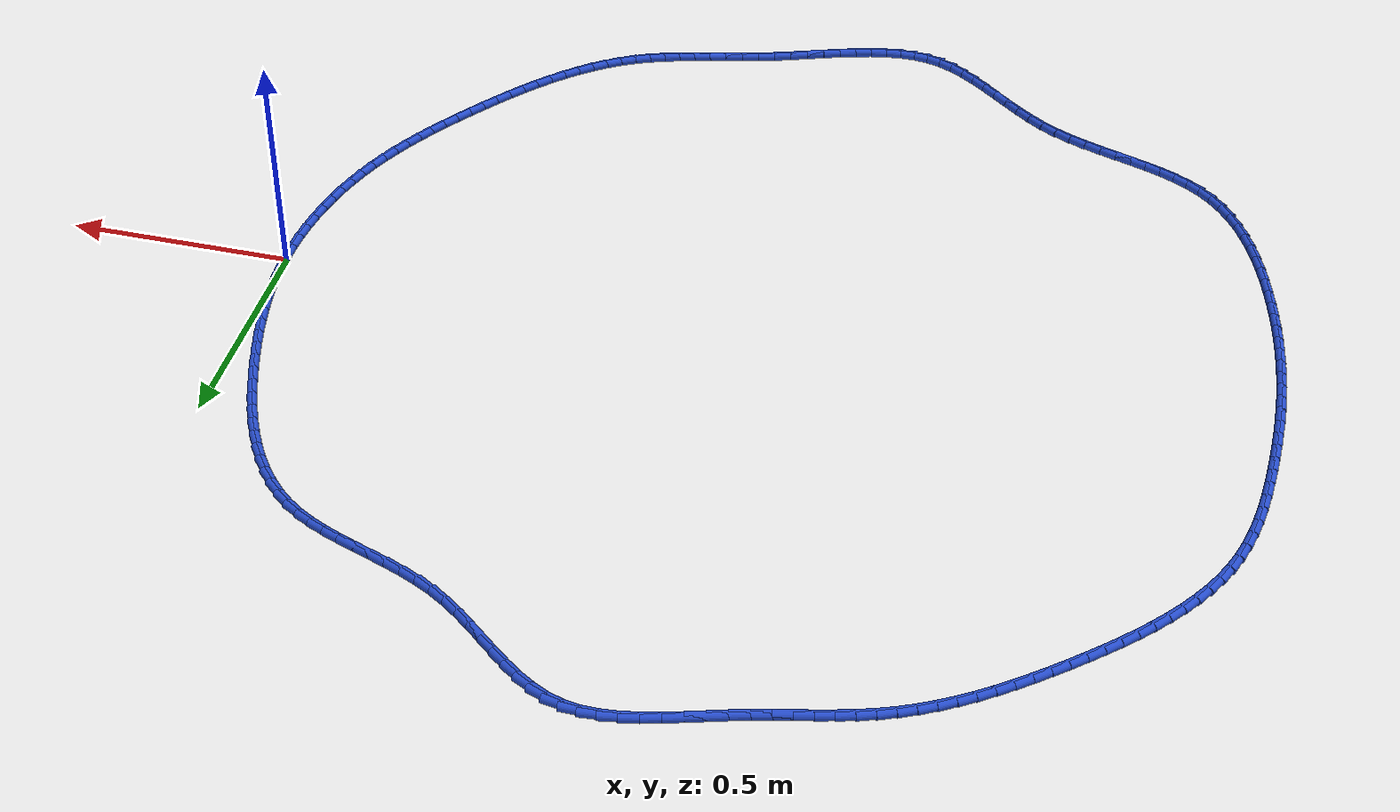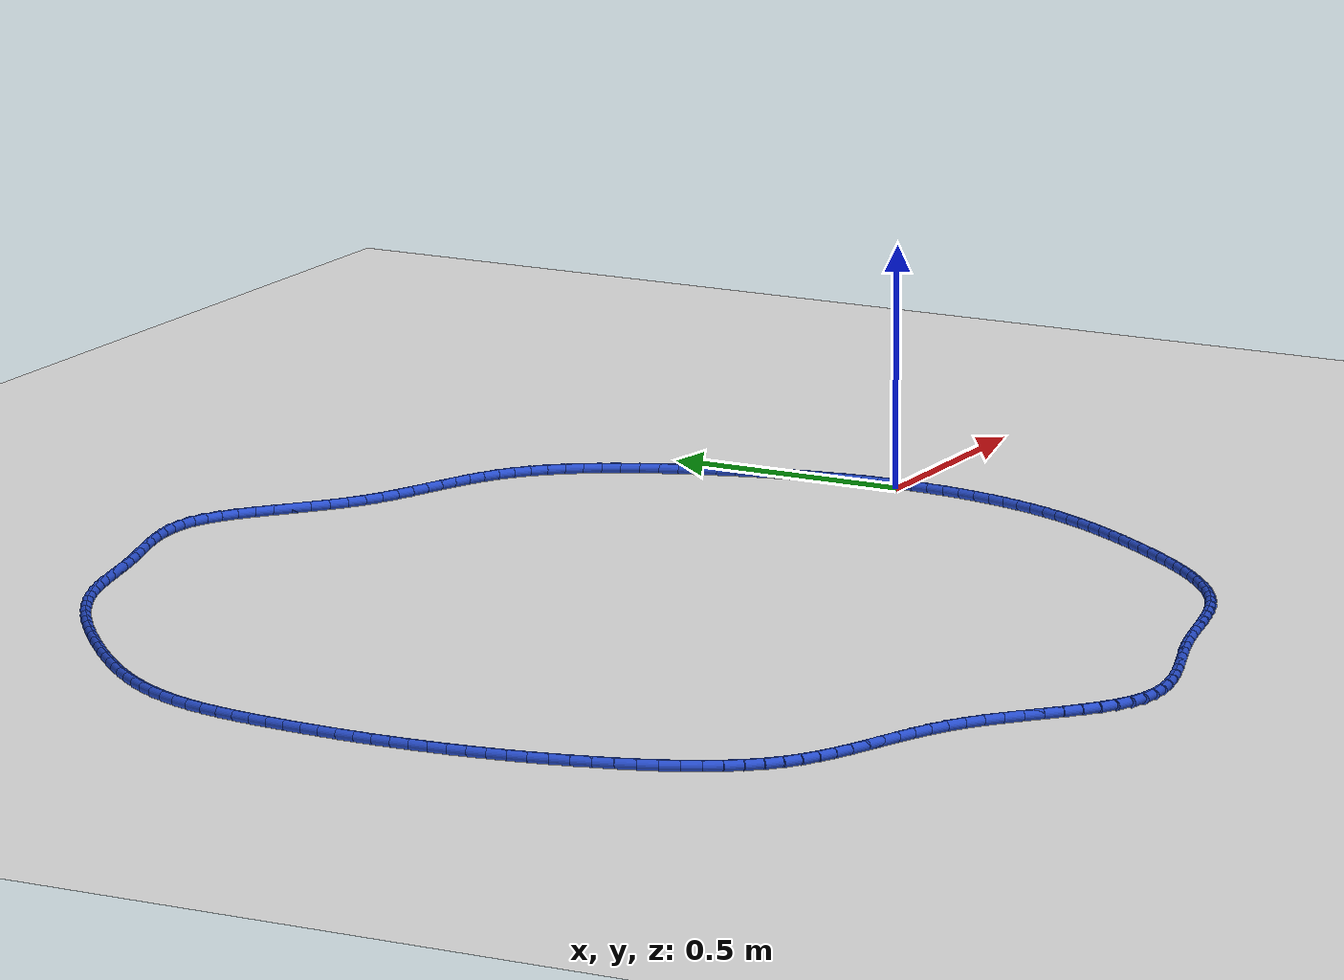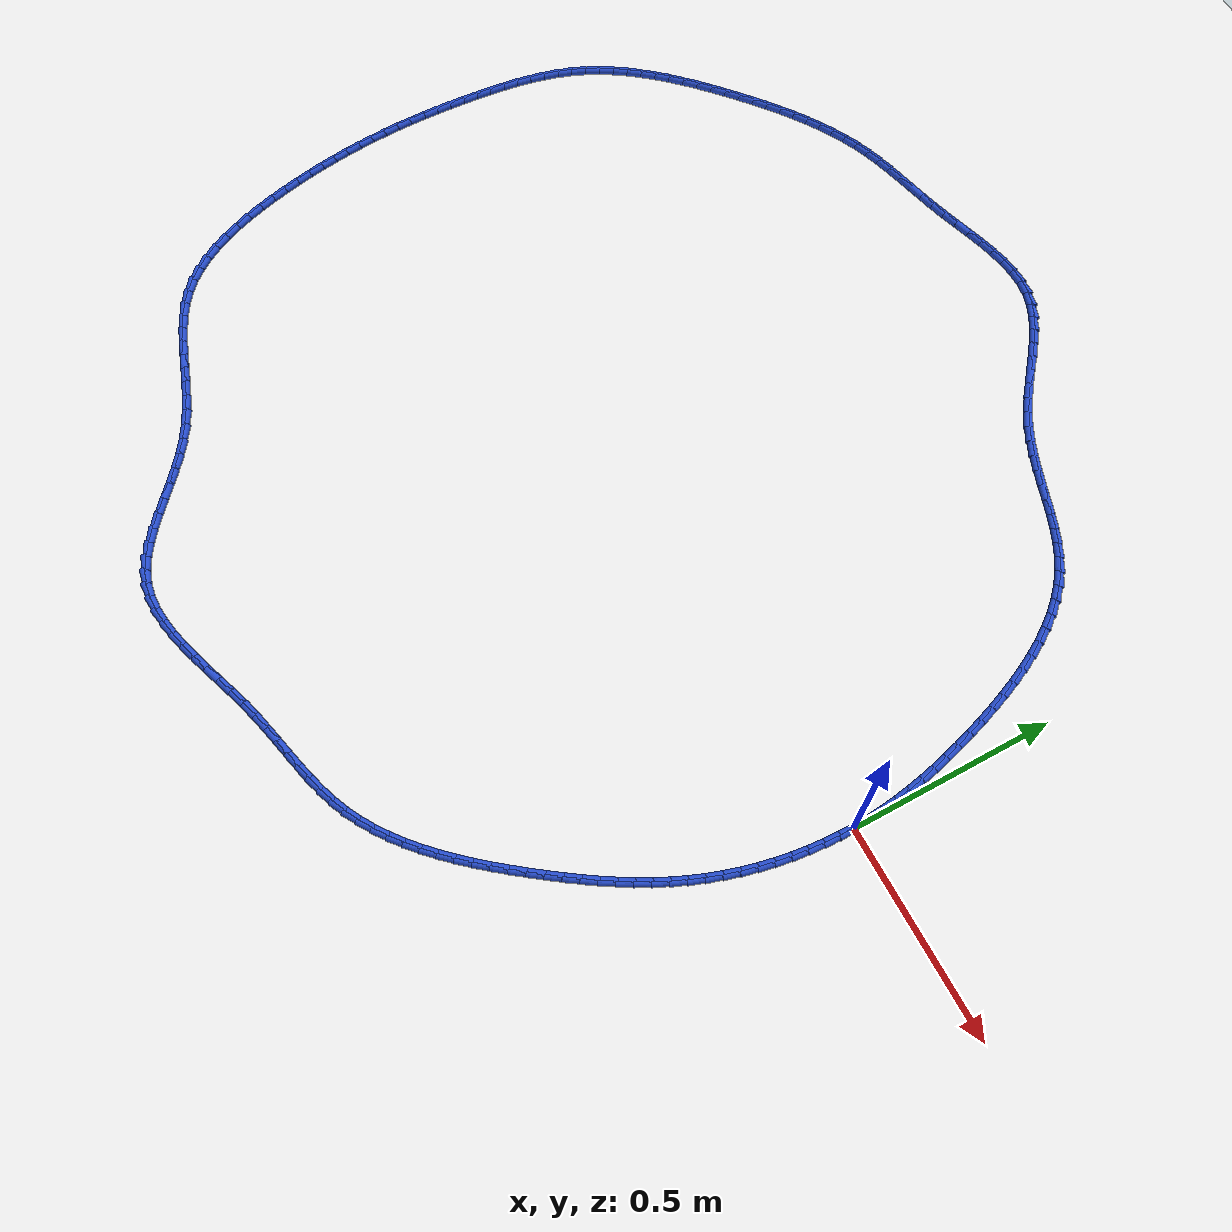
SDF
<sdf version="1.6">
 <world name="default">
  <light name="sun" type="directional">
   <pose>0 0 10 0 -0 0</pose>
   <diffuse>0.8 0.8 0.8 1</diffuse>
   <specular>0.2 0.2 0.2 1</specular>
   <attenuation>
    <range>1000</range>
    <constant>0.9</constant>
    <linear>0.01</linear>
    <quadratic>0.001</quadratic>
   </attenuation>
   <direction>-0.5 0.1 -0.9</direction>
  </light>
  <model name="ground_plane">
   <static>1</static>
   <link name="link">
    <collision name="collision">
     <geometry><plane><normal>0 0 1</normal><size>100 100</size></plane></geometry>
     <surface><friction><ode><mu>100</mu><mu2>50</mu2></ode></friction></surface>
    </collision>
    <visual name="visual">
     <cast_shadows>0</cast_shadows>
     <geometry><plane><normal>0 0 1</normal><size>100 100</size></plane></geometry>
     <material>
      <script><uri>file://media/materials/scripts/gazebo.material</uri><name>Gazebo/WhiteGlow</name></script>
     </material>
    </visual>
   </link>
  </model>
  <gravity>0 0 -9.8</gravity>
  <magnetic_field>6e-06 2.3e-05 -4.2e-05</magnetic_field>
  <atmosphere type="adiabatic"/>
  <physics name="default_physics" default="0" type="ode">
   <max_step_size>0.001</max_step_size>
   <real_time_factor>1</real_time_factor>
   <real_time_update_rate>1000</real_time_update_rate>
  </physics>
  <scene><ambient>0.4 0.4 0.4 1</ambient><background>0.7 0.7 0.7 1</background><shadows>1</shadows></scene>
  <spherical_coordinates>
   <surface_model>EARTH_WGS84</surface_model>
   <latitude_deg>0</latitude_deg>
   <longitude_deg>0</longitude_deg>
   <elevation>0</elevation>
   <heading_deg>0</heading_deg>
  </spherical_coordinates>
  <model name="line">
   <link name="link_0">
    <pose>2.42861286636753e-17 -3.469446951953614e-17 0.01 0 1.57 -1.5377557632998335</pose>
    <collision name="collision">
     <geometry><cylinder><radius>0.01</radius><length>0.08</length></cylinder></geometry>
    </collision>
    <visual name="visual">
     <material>
      <script><name>Gazebo/Blue</name><uri>file://media/materials/scripts/gazebo.material</uri></script>
     </material>
     <geometry><cylinder><radius>0.01</radius><length>0.08</length></cylinder></geometry>
    </visual>
   </link>
   <link name="link_1">
    <pose>-0.0012306059530227701 0.03723175338058333 0.01 0 1.57 -1.4981308171047736</pose>
    <collision name="collision">
     <geometry><cylinder><radius>0.01</radius><length>0.08</length></cylinder></geometry>
    </collision>
    <visual name="visual">
     <material>
      <script><name>Gazebo/Blue</name><uri>file://media/materials/scripts/gazebo.material</uri></script>
     </material>
     <geometry><cylinder><radius>0.01</radius><length>0.08</length></cylinder></geometry>
    </visual>
   </link>
   <link name="link_2">
    <pose>-0.003926080249354473 0.0742607146288759 0.01 0 1.57 -1.4605051240655114</pose>
    <collision name="collision">
     <geometry><cylinder><radius>0.01</radius><length>0.08</length></cylinder></geometry>
    </collision>
    <visual name="visual">
     <material>
      <script><name>Gazebo/Blue</name><uri>file://media/materials/scripts/gazebo.material</uri></script>
     </material>
     <geometry><cylinder><radius>0.01</radius><length>0.08</length></cylinder></geometry>
    </visual>
   </link>
   <link name="link_3">
    <pose>-0.0080105806420347 0.11114421353906367 0.01 0 1.57 -1.425140529627484</pose>
    <collision name="collision">
     <geometry><cylinder><radius>0.01</radius><length>0.08</length></cylinder></geometry>
    </collision>
    <visual name="visual">
     <material>
      <script><name>Gazebo/Blue</name><uri>file://media/materials/scripts/gazebo.material</uri></script>
     </material>
     <geometry><cylinder><radius>0.01</radius><length>0.08</length></cylinder></geometry>
    </visual>
   </link>
   <link name="link_4">
    <pose>-0.013408264884103072 0.14793957990533274 0.01 0 1.57 -1.3922448819460405</pose>
    <collision name="collision">
     <geometry><cylinder><radius>0.01</radius><length>0.08</length></cylinder></geometry>
    </collision>
    <visual name="visual">
     <material>
      <script><name>Gazebo/Blue</name><uri>file://media/materials/scripts/gazebo.material</uri></script>
     </material>
     <geometry><cylinder><radius>0.01</radius><length>0.08</length></cylinder></geometry>
    </visual>
   </link>
   <link name="link_5">
    <pose>-0.020043290728599214 0.18470414352186912 0.01 0 1.57 -1.3619722542262391</pose>
    <collision name="collision">
     <geometry><cylinder><radius>0.01</radius><length>0.08</length></cylinder></geometry>
    </collision>
    <visual name="visual">
     <material>
      <script><name>Gazebo/Blue</name><uri>file://media/materials/scripts/gazebo.material</uri></script>
     </material>
     <geometry><cylinder><radius>0.01</radius><length>0.08</length></cylinder></geometry>
    </visual>
   </link>
   <link name="link_6">
    <pose>-0.02783981592856273 0.22149523418285877 0.01 0 1.57 -1.3344259769714146</pose>
    <collision name="collision">
     <geometry><cylinder><radius>0.01</radius><length>0.08</length></cylinder></geometry>
    </collision>
    <visual name="visual">
     <material>
      <script><name>Gazebo/Blue</name><uri>file://media/materials/scripts/gazebo.material</uri></script>
     </material>
     <geometry><cylinder><radius>0.01</radius><length>0.08</length></cylinder></geometry>
    </visual>
   </link>
   <link name="link_7">
    <pose>-0.03672199823703327 0.25837018168248793 0.01 0 1.57 -1.309663646399887</pose>
    <collision name="collision">
     <geometry><cylinder><radius>0.01</radius><length>0.08</length></cylinder></geometry>
    </collision>
    <visual name="visual">
     <material>
      <script><name>Gazebo/Blue</name><uri>file://media/materials/scripts/gazebo.material</uri></script>
     </material>
     <geometry><cylinder><radius>0.01</radius><length>0.08</length></cylinder></geometry>
    </visual>
   </link>
   <link name="link_8">
    <pose>-0.046613995407050426 0.2953863158149424 0.01 0 1.57 -1.287703276062982</pose>
    <collision name="collision">
     <geometry><cylinder><radius>0.01</radius><length>0.08</length></cylinder></geometry>
    </collision>
    <visual name="visual">
     <material>
      <script><name>Gazebo/Blue</name><uri>file://media/materials/scripts/gazebo.material</uri></script>
     </material>
     <geometry><cylinder><radius>0.01</radius><length>0.08</length></cylinder></geometry>
    </visual>
   </link>
   <link name="link_9">
    <pose>-0.05743996519165384 0.33260096637440845 0.01 0 1.57 -1.2680426985150708</pose>
    <collision name="collision">
     <geometry><cylinder><radius>0.01</radius><length>0.08</length></cylinder></geometry>
    </collision>
    <visual name="visual">
     <material>
      <script><name>Gazebo/Blue</name><uri>file://media/materials/scripts/gazebo.material</uri></script>
     </material>
     <geometry><cylinder><radius>0.01</radius><length>0.08</length></cylinder></geometry>
    </visual>
   </link>
   <link name="link_10">
    <pose>-0.06913681231028376 0.37004813887499416 0.01 0 1.57 -1.2463307773022332</pose>
    <collision name="collision">
     <geometry><cylinder><radius>0.01</radius><length>0.08</length></cylinder></geometry>
    </collision>
    <visual name="visual">
     <material>
      <script><name>Gazebo/Blue</name><uri>file://media/materials/scripts/gazebo.material</uri></script>
     </material>
     <geometry><cylinder><radius>0.01</radius><length>0.08</length></cylinder></geometry>
    </visual>
   </link>
   <link name="link_11">
    <pose>-0.08175316042639008 0.40755741655038663 0.01 0 1.57 -1.220121021606591</pose>
    <collision name="collision">
     <geometry><cylinder><radius>0.01</radius><length>0.08</length></cylinder></geometry>
    </collision>
    <visual name="visual">
     <material>
      <script><name>Gazebo/Blue</name><uri>file://media/materials/scripts/gazebo.material</uri></script>
     </material>
     <geometry><cylinder><radius>0.01</radius><length>0.08</length></cylinder></geometry>
    </visual>
   </link>
   <link name="link_12">
    <pose>-0.09539548594241155 0.44485252423274974 0.01 0 1.57 -1.1890313534579608</pose>
    <collision name="collision">
     <geometry><cylinder><radius>0.01</radius><length>0.08</length></cylinder></geometry>
    </collision>
    <visual name="visual">
     <material>
      <script><name>Gazebo/Blue</name><uri>file://media/materials/scripts/gazebo.material</uri></script>
     </material>
     <geometry><cylinder><radius>0.01</radius><length>0.08</length></cylinder></geometry>
    </visual>
   </link>
   <link name="link_13">
    <pose>-0.11017075329953971 0.4816562937454951 0.01 0 1.57 -1.1525835578874646</pose>
    <collision name="collision">
     <geometry><cylinder><radius>0.01</radius><length>0.08</length></cylinder></geometry>
    </collision>
    <visual name="visual">
     <material>
      <script><name>Gazebo/Blue</name><uri>file://media/materials/scripts/gazebo.material</uri></script>
     </material>
     <geometry><cylinder><radius>0.01</radius><length>0.08</length></cylinder></geometry>
    </visual>
   </link>
   <link name="link_14">
    <pose>-0.1261859269389661 0.5176915569120346 0.01 0 1.57 -1.1101885092594088</pose>
    <collision name="collision">
     <geometry><cylinder><radius>0.01</radius><length>0.08</length></cylinder></geometry>
    </collision>
    <visual name="visual">
     <material>
      <script><name>Gazebo/Blue</name><uri>file://media/materials/scripts/gazebo.material</uri></script>
     </material>
     <geometry><cylinder><radius>0.01</radius><length>0.08</length></cylinder></geometry>
    </visual>
   </link>
   <link name="link_15">
    <pose>-0.14354797130188227 0.55268114555578 0.01 0 1.57 -1.0611563104371302</pose>
    <collision name="collision">
     <geometry><cylinder><radius>0.01</radius><length>0.08</length></cylinder></geometry>
    </collision>
    <visual name="visual">
     <material>
      <script><name>Gazebo/Blue</name><uri>file://media/materials/scripts/gazebo.material</uri></script>
     </material>
     <geometry><cylinder><radius>0.01</radius><length>0.08</length></cylinder></geometry>
    </visual>
   </link>
   <link name="link_16">
    <pose>-0.1623638508294796 0.5863478915001425 0.01 0 1.57 -1.0047205085807145</pose>
    <collision name="collision">
     <geometry><cylinder><radius>0.01</radius><length>0.08</length></cylinder></geometry>
    </collision>
    <visual name="visual">
     <material>
      <script><name>Gazebo/Blue</name><uri>file://media/materials/scripts/gazebo.material</uri></script>
     </material>
     <geometry><cylinder><radius>0.01</radius><length>0.08</length></cylinder></geometry>
    </visual>
   </link>
   <link name="link_17">
    <pose>-0.18274052996294976 0.6184146265685346 0.01 0 1.57 -0.9400874756557059</pose>
    <collision name="collision">
     <geometry><cylinder><radius>0.01</radius><length>0.08</length></cylinder></geometry>
    </collision>
    <visual name="visual">
     <material>
      <script><name>Gazebo/Blue</name><uri>file://media/materials/scripts/gazebo.material</uri></script>
     </material>
     <geometry><cylinder><radius>0.01</radius><length>0.08</length></cylinder></geometry>
    </visual>
   </link>
   <link name="link_18">
    <pose>-0.2047849731434842 0.6486041825843674 0.01 0 1.57 -0.8665250352226699</pose>
    <collision name="collision">
     <geometry><cylinder><radius>0.01</radius><length>0.08</length></cylinder></geometry>
    </collision>
    <visual name="visual">
     <material>
      <script><name>Gazebo/Blue</name><uri>file://media/materials/scripts/gazebo.material</uri></script>
     </material>
     <geometry><cylinder><radius>0.01</radius><length>0.08</length></cylinder></geometry>
    </visual>
   </link>
   <link name="link_19">
    <pose>-0.22860414481227453 0.6766393913710528 0.01 0 1.57 -0.7835041581682417</pose>
    <collision name="collision">
     <geometry><cylinder><radius>0.01</radius><length>0.08</length></cylinder></geometry>
    </collision>
    <visual name="visual">
     <material>
      <script><name>Gazebo/Blue</name><uri>file://media/materials/scripts/gazebo.material</uri></script>
     </material>
     <geometry><cylinder><radius>0.01</radius><length>0.08</length></cylinder></geometry>
    </visual>
   </link>
   <link name="link_20">
    <pose>-0.2543050094105123 0.7022430847520031 0.01 0 1.57 -0.6908982940790531</pose>
    <collision name="collision">
     <geometry><cylinder><radius>0.01</radius><length>0.08</length></cylinder></geometry>
    </collision>
    <visual name="visual">
     <material>
      <script><name>Gazebo/Blue</name><uri>file://media/materials/scripts/gazebo.material</uri></script>
     </material>
     <geometry><cylinder><radius>0.01</radius><length>0.08</length></cylinder></geometry>
    </visual>
   </link>
   <link name="link_21">
    <pose>-0.2819945313793889 0.7251380945506293 0.01 0 1.57 -0.5905024079407324</pose>
    <collision name="collision">
     <geometry><cylinder><radius>0.01</radius><length>0.08</length></cylinder></geometry>
    </collision>
    <visual name="visual">
     <material>
      <script><name>Gazebo/Blue</name><uri>file://media/materials/scripts/gazebo.material</uri></script>
     </material>
     <geometry><cylinder><radius>0.01</radius><length>0.08</length></cylinder></geometry>
    </visual>
   </link>
   <link name="link_22">
    <pose>-0.3117585735056314 0.7450884417860737 0.01 0 1.57 -0.49927831312667775</pose>
    <collision name="collision">
     <geometry><cylinder><radius>0.01</radius><length>0.08</length></cylinder></geometry>
    </collision>
    <visual name="visual">
     <material>
      <script><name>Gazebo/Blue</name><uri>file://media/materials/scripts/gazebo.material</uri></script>
     </material>
     <geometry><cylinder><radius>0.01</radius><length>0.08</length></cylinder></geometry>
    </visual>
   </link>
   <link name="link_23">
    <pose>-0.3434264088022716 0.7623589957132814 0.01 0 1.57 -0.42874688198876476</pose>
    <collision name="collision">
     <geometry><cylinder><radius>0.01</radius><length>0.08</length></cylinder></geometry>
    </collision>
    <visual name="visual">
     <material>
      <script><name>Gazebo/Blue</name><uri>file://media/materials/scripts/gazebo.material</uri></script>
     </material>
     <geometry><cylinder><radius>0.01</radius><length>0.08</length></cylinder></geometry>
    </visual>
   </link>
   <link name="link_24">
    <pose>-0.37665624843168866 0.7775485283179215 0.01 0 1.57 -0.37886797641526837</pose>
    <collision name="collision">
     <geometry><cylinder><radius>0.01</radius><length>0.08</length></cylinder></geometry>
    </collision>
    <visual name="visual">
     <material>
      <script><name>Gazebo/Blue</name><uri>file://media/materials/scripts/gazebo.material</uri></script>
     </material>
     <geometry><cylinder><radius>0.01</radius><length>0.08</length></cylinder></geometry>
    </visual>
   </link>
   <link name="link_25">
    <pose>-0.411103193939364 0.7912618813760336 0.01 0 1.57 -0.3487381682582309</pose>
    <collision name="collision">
     <geometry><cylinder><radius>0.01</radius><length>0.08</length></cylinder></geometry>
    </collision>
    <visual name="visual">
     <material>
      <script><name>Gazebo/Blue</name><uri>file://media/materials/scripts/gazebo.material</uri></script>
     </material>
     <geometry><cylinder><radius>0.01</radius><length>0.08</length></cylinder></geometry>
    </visual>
   </link>
   <link name="link_26">
    <pose>-0.4464223468707784 0.8041038966636568 0.01 0 1.57 -0.33740175488924795</pose>
    <collision name="collision">
     <geometry><cylinder><radius>0.01</radius><length>0.08</length></cylinder></geometry>
    </collision>
    <visual name="visual">
     <material>
      <script><name>Gazebo/Blue</name><uri>file://media/materials/scripts/gazebo.material</uri></script>
     </material>
     <geometry><cylinder><radius>0.01</radius><length>0.08</length></cylinder></geometry>
    </visual>
   </link>
   <link name="link_27">
    <pose>-0.482268808771413 0.8166794159568307 0.01 0 1.57 -0.3441659068617075</pose>
    <collision name="collision">
     <geometry><cylinder><radius>0.01</radius><length>0.08</length></cylinder></geometry>
    </collision>
    <visual name="visual">
     <material>
      <script><name>Gazebo/Blue</name><uri>file://media/materials/scripts/gazebo.material</uri></script>
     </material>
     <geometry><cylinder><radius>0.01</radius><length>0.08</length></cylinder></geometry>
    </visual>
   </link>
   <link name="link_28">
    <pose>-0.518297681186749 0.8295932810315947 0.01 0 1.57 -0.3686858567018237</pose>
    <collision name="collision">
     <geometry><cylinder><radius>0.01</radius><length>0.08</length></cylinder></geometry>
    </collision>
    <visual name="visual">
     <material>
      <script><name>Gazebo/Blue</name><uri>file://media/materials/scripts/gazebo.material</uri></script>
     </material>
     <geometry><cylinder><radius>0.01</radius><length>0.08</length></cylinder></geometry>
    </visual>
   </link>
   <link name="link_29">
    <pose>-0.5541640656622675 0.8434503336639881 0.01 0 1.57 -0.41087881208877697</pose>
    <collision name="collision">
     <geometry><cylinder><radius>0.01</radius><length>0.08</length></cylinder></geometry>
    </collision>
    <visual name="visual">
     <material>
      <script><name>Gazebo/Blue</name><uri>file://media/materials/scripts/gazebo.material</uri></script>
     </material>
     <geometry><cylinder><radius>0.01</radius><length>0.08</length></cylinder></geometry>
    </visual>
   </link>
   <link name="link_30">
    <pose>-0.5895230637434492 0.8588554156300501 0.01 0 1.57 -0.47068437874454233</pose>
    <collision name="collision">
     <geometry><cylinder><radius>0.01</radius><length>0.08</length></cylinder></geometry>
    </collision>
    <visual name="visual">
     <material>
      <script><name>Gazebo/Blue</name><uri>file://media/materials/scripts/gazebo.material</uri></script>
     </material>
     <geometry><cylinder><radius>0.01</radius><length>0.08</length></cylinder></geometry>
    </visual>
   </link>
   <link name="link_31">
    <pose>-0.6240297769757756 0.8764133687058208 0.01 0 1.57 -0.5465471982181477</pose>
    <collision name="collision">
     <geometry><cylinder><radius>0.01</radius><length>0.08</length></cylinder></geometry>
    </collision>
    <visual name="visual">
     <material>
      <script><name>Gazebo/Blue</name><uri>file://media/materials/scripts/gazebo.material</uri></script>
     </material>
     <geometry><cylinder><radius>0.01</radius><length>0.08</length></cylinder></geometry>
    </visual>
   </link>
   <link name="link_32">
    <pose>-0.6573564013776125 0.8966881047991677 0.01 0 1.57 -0.6168525762348066</pose>
    <collision name="collision">
     <geometry><cylinder><radius>0.01</radius><length>0.08</length></cylinder></geometry>
    </collision>
    <visual name="visual">
     <material>
      <script><name>Gazebo/Blue</name><uri>file://media/materials/scripts/gazebo.material</uri></script>
     </material>
     <geometry><cylinder><radius>0.01</radius><length>0.08</length></cylinder></geometry>
    </visual>
   </link>
   <link name="link_33">
    <pose>-0.6894943214918186 0.919479292058185 0.01 0 1.57 -0.6639362488759559</pose>
    <collision name="collision">
     <geometry><cylinder><radius>0.01</radius><length>0.08</length></cylinder></geometry>
    </collision>
    <visual name="visual">
     <material>
      <script><name>Gazebo/Blue</name><uri>file://media/materials/scripts/gazebo.material</uri></script>
     </material>
     <geometry><cylinder><radius>0.01</radius><length>0.08</length></cylinder></geometry>
    </visual>
   </link>
   <link name="link_34">
    <pose>-0.7207177274639663 0.9439094677176673 0.01 0 1.57 -0.6884206580190309</pose>
    <collision name="collision">
     <geometry><cylinder><radius>0.01</radius><length>0.08</length></cylinder></geometry>
    </collision>
    <visual name="visual">
     <material>
      <script><name>Gazebo/Blue</name><uri>file://media/materials/scripts/gazebo.material</uri></script>
     </material>
     <geometry><cylinder><radius>0.01</radius><length>0.08</length></cylinder></geometry>
    </visual>
   </link>
   <link name="link_35">
    <pose>-0.7513105939026653 0.9690777417453091 0.01 0 1.57 -0.6908277154732276</pose>
    <collision name="collision">
     <geometry><cylinder><radius>0.01</radius><length>0.08</length></cylinder></geometry>
    </collision>
    <visual name="visual">
     <material>
      <script><name>Gazebo/Blue</name><uri>file://media/materials/scripts/gazebo.material</uri></script>
     </material>
     <geometry><cylinder><radius>0.01</radius><length>0.08</length></cylinder></geometry>
    </visual>
   </link>
   <link name="link_36">
    <pose>-0.7815568954165251 0.9940832241088046 0.01 0 1.57 -0.6705824713510131</pose>
    <collision name="collision">
     <geometry><cylinder><radius>0.01</radius><length>0.08</length></cylinder></geometry>
    </collision>
    <visual name="visual">
     <material>
      <script><name>Gazebo/Blue</name><uri>file://media/materials/scripts/gazebo.material</uri></script>
     </material>
     <geometry><cylinder><radius>0.01</radius><length>0.08</length></cylinder></geometry>
    </visual>
   </link>
   <link name="link_37">
    <pose>-0.8117406066141545 1.018025024775848 0.01 0 1.57 -0.6258738531762549</pose>
    <collision name="collision">
     <geometry><cylinder><radius>0.01</radius><length>0.08</length></cylinder></geometry>
    </collision>
    <visual name="visual">
     <material>
      <script><name>Gazebo/Blue</name><uri>file://media/materials/scripts/gazebo.material</uri></script>
     </material>
     <geometry><cylinder><radius>0.01</radius><length>0.08</length></cylinder></geometry>
    </visual>
   </link>
   <link name="link_38">
    <pose>-0.8421457021041638 1.0400022537141342 0.01 0 1.57 -0.5537629203544503</pose>
    <collision name="collision">
     <geometry><cylinder><radius>0.01</radius><length>0.08</length></cylinder></geometry>
    </collision>
    <visual name="visual">
     <material>
      <script><name>Gazebo/Blue</name><uri>file://media/materials/scripts/gazebo.material</uri></script>
     </material>
     <geometry><cylinder><radius>0.01</radius><length>0.08</length></cylinder></geometry>
    </visual>
   </link>
   <link name="link_39">
    <pose>-0.8730561564951621 1.0591140208913574 0.01 0 1.57 -0.45083534108492157</pose>
    <collision name="collision">
     <geometry><cylinder><radius>0.01</radius><length>0.08</length></cylinder></geometry>
    </collision>
    <visual name="visual">
     <material>
      <script><name>Gazebo/Blue</name><uri>file://media/materials/scripts/gazebo.material</uri></script>
     </material>
     <geometry><cylinder><radius>0.01</radius><length>0.08</length></cylinder></geometry>
    </visual>
   </link>
   <link name="link_40">
    <pose>-0.904755944395759 1.074459436275212 0.01 0 1.57 -0.3149745797117194</pose>
    <collision name="collision">
     <geometry><cylinder><radius>0.01</radius><length>0.08</length></cylinder></geometry>
    </collision>
    <visual name="visual">
     <material>
      <script><name>Gazebo/Blue</name><uri>file://media/materials/scripts/gazebo.material</uri></script>
     </material>
     <geometry><cylinder><radius>0.01</radius><length>0.08</length></cylinder></geometry>
    </visual>
   </link>
   <link name="link_41">
    <pose>-0.9375290404145633 1.085137609833392 0.01 0 1.57 -0.15445070433973135</pose>
    <collision name="collision">
     <geometry><cylinder><radius>0.01</radius><length>0.08</length></cylinder></geometry>
    </collision>
    <visual name="visual">
     <material>
      <script><name>Gazebo/Blue</name><uri>file://media/materials/scripts/gazebo.material</uri></script>
     </material>
     <geometry><cylinder><radius>0.01</radius><length>0.08</length></cylinder></geometry>
    </visual>
   </link>
   <link name="link_42">
    <pose>-0.9716039636044332 1.0904427577645868 0.01 0 1.57 -0.010237912246959335</pose>
    <collision name="collision">
     <geometry><cylinder><radius>0.01</radius><length>0.08</length></cylinder></geometry>
    </collision>
    <visual name="visual">
     <material>
      <script><name>Gazebo/Blue</name><uri>file://media/materials/scripts/gazebo.material</uri></script>
     </material>
     <geometry><cylinder><radius>0.01</radius><length>0.08</length></cylinder></geometry>
    </visual>
   </link>
   <link name="link_43">
    <pose>-1.0068866587633527 1.0908039915224352 0.01 0 1.57 0.10284120702126016</pose>
    <collision name="collision">
     <geometry><cylinder><radius>0.01</radius><length>0.08</length></cylinder></geometry>
    </collision>
    <visual name="visual">
     <material>
      <script><name>Gazebo/Blue</name><uri>file://media/materials/scripts/gazebo.material</uri></script>
     </material>
     <geometry><cylinder><radius>0.01</radius><length>0.08</length></cylinder></geometry>
    </visual>
   </link>
   <link name="link_44">
    <pose>-1.0431667422989725 1.0870596943366468 0.01 0 1.57 0.1869332416069128</pose>
    <collision name="collision">
     <geometry><cylinder><radius>0.01</radius><length>0.08</length></cylinder></geometry>
    </collision>
    <visual name="visual">
     <material>
      <script><name>Gazebo/Blue</name><uri>file://media/materials/scripts/gazebo.material</uri></script>
     </material>
     <geometry><cylinder><radius>0.01</radius><length>0.08</length></cylinder></geometry>
    </visual>
   </link>
   <link name="link_45">
    <pose>-1.0802336745102745 1.0800487986654752 0.01 0 1.57 0.24567239808402153</pose>
    <collision name="collision">
     <geometry><cylinder><radius>0.01</radius><length>0.08</length></cylinder></geometry>
    </collision>
    <visual name="visual">
     <material>
      <script><name>Gazebo/Blue</name><uri>file://media/materials/scripts/gazebo.material</uri></script>
     </material>
     <geometry><cylinder><radius>0.01</radius><length>0.08</length></cylinder></geometry>
    </visual>
   </link>
   <link name="link_46">
    <pose>-1.1178769156962396 1.0706102369671717 0.01 0 1.57 0.2823710493330009</pose>
    <collision name="collision">
     <geometry><cylinder><radius>0.01</radius><length>0.08</length></cylinder></geometry>
    </collision>
    <visual name="visual">
     <material>
      <script><name>Gazebo/Blue</name><uri>file://media/materials/scripts/gazebo.material</uri></script>
     </material>
     <geometry><cylinder><radius>0.01</radius><length>0.08</length></cylinder></geometry>
    </visual>
   </link>
   <link name="link_47">
    <pose>-1.1558859261558487 1.0595829416999898 0.01 0 1.57 0.29931862418804644</pose>
    <collision name="collision">
     <geometry><cylinder><radius>0.01</radius><length>0.08</length></cylinder></geometry>
    </collision>
    <visual name="visual">
     <material>
      <script><name>Gazebo/Blue</name><uri>file://media/materials/scripts/gazebo.material</uri></script>
     </material>
     <geometry><cylinder><radius>0.01</radius><length>0.08</length></cylinder></geometry>
    </visual>
   </link>
   <link name="link_48">
    <pose>-1.1940501661880838 1.0478058453221826 0.01 0 1.57 0.2975911426088817</pose>
    <collision name="collision">
     <geometry><cylinder><radius>0.01</radius><length>0.08</length></cylinder></geometry>
    </collision>
    <visual name="visual">
     <material>
      <script><name>Gazebo/Blue</name><uri>file://media/materials/scripts/gazebo.material</uri></script>
     </material>
     <geometry><cylinder><radius>0.01</radius><length>0.08</length></cylinder></geometry>
    </visual>
   </link>
   <link name="link_49">
    <pose>-1.232159096091926 1.0361178802920024 0.01 0 1.57 0.2776125273438024</pose>
    <collision name="collision">
     <geometry><cylinder><radius>0.01</radius><length>0.08</length></cylinder></geometry>
    </collision>
    <visual name="visual">
     <material>
      <script><name>Gazebo/Blue</name><uri>file://media/materials/scripts/gazebo.material</uri></script>
     </material>
     <geometry><cylinder><radius>0.01</radius><length>0.08</length></cylinder></geometry>
    </visual>
   </link>
   <link name="link_50">
    <pose>-1.2700052946151772 1.025332803401851 0.01 0 1.57 0.25323413614008616</pose>
    <collision name="collision">
     <geometry><cylinder><radius>0.01</radius><length>0.08</length></cylinder></geometry>
    </collision>
    <visual name="visual">
     <material>
      <script><name>Gazebo/Blue</name><uri>file://media/materials/scripts/gazebo.material</uri></script>
     </material>
     <geometry><cylinder><radius>0.01</radius><length>0.08</length></cylinder></geometry>
    </visual>
   </link>
   <link name="link_51">
    <pose>-1.3074586478881973 1.0156402583214854 0.01 0 1.57 0.2400868211530857</pose>
    <collision name="collision">
     <geometry><cylinder><radius>0.01</radius><length>0.08</length></cylinder></geometry>
    </collision>
    <visual name="visual">
     <material>
      <script><name>Gazebo/Blue</name><uri>file://media/materials/scripts/gazebo.material</uri></script>
     </material>
     <geometry><cylinder><radius>0.01</radius><length>0.08</length></cylinder></geometry>
    </visual>
   </link>
   <link name="link_52">
    <pose>-1.344469584534965 1.0065796581018849 0.01 0 1.57 0.23953303718060182</pose>
    <collision name="collision">
     <geometry><cylinder><radius>0.01</radius><length>0.08</length></cylinder></geometry>
    </collision>
    <visual name="visual">
     <material>
      <script><name>Gazebo/Blue</name><uri>file://media/materials/scripts/gazebo.material</uri></script>
     </material>
     <geometry><cylinder><radius>0.01</radius><length>0.08</length></cylinder></geometry>
    </visual>
   </link>
   <link name="link_53">
    <pose>-1.3809922989913888 0.9976600138768246 0.01 0 1.57 0.25209243304709616</pose>
    <collision name="collision">
     <geometry><cylinder><radius>0.01</radius><length>0.08</length></cylinder></geometry>
    </collision>
    <visual name="visual">
     <material>
      <script><name>Gazebo/Blue</name><uri>file://media/materials/scripts/gazebo.material</uri></script>
     </material>
     <geometry><cylinder><radius>0.01</radius><length>0.08</length></cylinder></geometry>
    </visual>
   </link>
   <link name="link_54">
    <pose>-1.416980985693379 0.988390336780079 0.01 0 1.57 0.27813995150906007</pose>
    <collision name="collision">
     <geometry><cylinder><radius>0.01</radius><length>0.08</length></cylinder></geometry>
    </collision>
    <visual name="visual">
     <material>
      <script><name>Gazebo/Blue</name><uri>file://media/materials/scripts/gazebo.material</uri></script>
     </material>
     <geometry><cylinder><radius>0.01</radius><length>0.08</length></cylinder></geometry>
    </visual>
   </link>
   <link name="link_55">
    <pose>-1.4523898390768453 0.9782796379454224 0.01 0 1.57 0.3178203825866348</pose>
    <collision name="collision">
     <geometry><cylinder><radius>0.01</radius><length>0.08</length></cylinder></geometry>
    </collision>
    <visual name="visual">
     <material>
      <script><name>Gazebo/Blue</name><uri>file://media/materials/scripts/gazebo.material</uri></script>
     </material>
     <geometry><cylinder><radius>0.01</radius><length>0.08</length></cylinder></geometry>
    </visual>
   </link>
   <link name="link_56">
    <pose>-1.4871730535776966 0.9668369285066293 0.01 0 1.57 0.3703688471670377</pose>
    <collision name="collision">
     <geometry><cylinder><radius>0.01</radius><length>0.08</length></cylinder></geometry>
    </collision>
    <visual name="visual">
     <material>
      <script><name>Gazebo/Blue</name><uri>file://media/materials/scripts/gazebo.material</uri></script>
     </material>
     <geometry><cylinder><radius>0.01</radius><length>0.08</length></cylinder></geometry>
    </visual>
   </link>
   <link name="link_57">
    <pose>-1.5212873865819019 0.953590757447348 0.01 0 1.57 0.4261487031263551</pose>
    <collision name="collision">
     <geometry><cylinder><radius>0.01</radius><length>0.08</length></cylinder></geometry>
    </collision>
    <visual name="visual">
     <material>
      <script><name>Gazebo/Blue</name><uri>file://media/materials/scripts/gazebo.material</uri></script>
     </material>
     <geometry><cylinder><radius>0.01</radius><length>0.08</length></cylinder></geometry>
    </visual>
   </link>
   <link name="link_58">
    <pose>-1.5547338628133085 0.9384071319856674 0.01 0 1.57 0.4772437791033624</pose>
    <collision name="collision">
     <geometry><cylinder><radius>0.01</radius><length>0.08</length></cylinder></geometry>
    </collision>
    <visual name="visual">
     <material>
      <script><name>Gazebo/Blue</name><uri>file://media/materials/scripts/gazebo.material</uri></script>
     </material>
     <geometry><cylinder><radius>0.01</radius><length>0.08</length></cylinder></geometry>
    </visual>
   </link>
   <link name="link_59">
    <pose>-1.5875508895979857 0.9214370339405707 0.01 0 1.57 0.5233726154518015</pose>
    <collision name="collision">
     <geometry><cylinder><radius>0.01</radius><length>0.08</length></cylinder></geometry>
    </collision>
    <visual name="visual">
     <material>
      <script><name>Gazebo/Blue</name><uri>file://media/materials/scripts/gazebo.material</uri></script>
     </material>
     <geometry><cylinder><radius>0.01</radius><length>0.08</length></cylinder></geometry>
    </visual>
   </link>
   <link name="link_60">
    <pose>-1.6197780479189703 0.9028403921386134 0.01 0 1.57 0.564597298871546</pose>
    <collision name="collision">
     <geometry><cylinder><radius>0.01</radius><length>0.08</length></cylinder></geometry>
    </collision>
    <visual name="visual">
     <material>
      <script><name>Gazebo/Blue</name><uri>file://media/materials/scripts/gazebo.material</uri></script>
     </material>
     <geometry><cylinder><radius>0.01</radius><length>0.08</length></cylinder></geometry>
    </visual>
   </link>
   <link name="link_61">
    <pose>-1.6514549187592953 0.88277713540635 0.01 0 1.57 0.6010488464074891</pose>
    <collision name="collision">
     <geometry><cylinder><radius>0.01</radius><length>0.08</length></cylinder></geometry>
    </collision>
    <visual name="visual">
     <material>
      <script><name>Gazebo/Blue</name><uri>file://media/materials/scripts/gazebo.material</uri></script>
     </material>
     <geometry><cylinder><radius>0.01</radius><length>0.08</length></cylinder></geometry>
    </visual>
   </link>
   <link name="link_62">
    <pose>-1.6826210831019974 0.8614071925703365 0.01 0 1.57 0.6328972225329598</pose>
    <collision name="collision">
     <geometry><cylinder><radius>0.01</radius><length>0.08</length></cylinder></geometry>
    </collision>
    <visual name="visual">
     <material>
      <script><name>Gazebo/Blue</name><uri>file://media/materials/scripts/gazebo.material</uri></script>
     </material>
     <geometry><cylinder><radius>0.01</radius><length>0.08</length></cylinder></geometry>
    </visual>
   </link>
   <link name="link_63">
    <pose>-1.7133161219301112 0.8388904924571268 0.01 0 1.57 0.6603274313719758</pose>
    <collision name="collision">
     <geometry><cylinder><radius>0.01</radius><length>0.08</length></cylinder></geometry>
    </collision>
    <visual name="visual">
     <material>
      <script><name>Gazebo/Blue</name><uri>file://media/materials/scripts/gazebo.material</uri></script>
     </material>
     <geometry><cylinder><radius>0.01</radius><length>0.08</length></cylinder></geometry>
    </visual>
   </link>
   <link name="link_64">
    <pose>-1.743579616226671 0.8153869638932765 0.01 0 1.57 0.6835214183278648</pose>
    <collision name="collision">
     <geometry><cylinder><radius>0.01</radius><length>0.08</length></cylinder></geometry>
    </collision>
    <visual name="visual">
     <material>
      <script><name>Gazebo/Blue</name><uri>file://media/materials/scripts/gazebo.material</uri></script>
     </material>
     <geometry><cylinder><radius>0.01</radius><length>0.08</length></cylinder></geometry>
    </visual>
   </link>
   <link name="link_65">
    <pose>-1.7734511469747116 0.7910565357053404 0.01 0 1.57 0.7026448909877253</pose>
    <collision name="collision">
     <geometry><cylinder><radius>0.01</radius><length>0.08</length></cylinder></geometry>
    </collision>
    <visual name="visual">
     <material>
      <script><name>Gazebo/Blue</name><uri>file://media/materials/scripts/gazebo.material</uri></script>
     </material>
     <geometry><cylinder><radius>0.01</radius><length>0.08</length></cylinder></geometry>
    </visual>
   </link>
   <link name="link_66">
    <pose>-1.8029702951572697 0.7660591367198734 0.01 0 1.57 0.7181065279051181</pose>
    <collision name="collision">
     <geometry><cylinder><radius>0.01</radius><length>0.08</length></cylinder></geometry>
    </collision>
    <visual name="visual">
     <material>
      <script><name>Gazebo/Blue</name><uri>file://media/materials/scripts/gazebo.material</uri></script>
     </material>
     <geometry><cylinder><radius>0.01</radius><length>0.08</length></cylinder></geometry>
    </visual>
   </link>
   <link name="link_67">
    <pose>-1.8321691155087407 0.740547443304567 0.01 0 1.57 0.7343392273941438</pose>
    <collision name="collision">
     <geometry><cylinder><radius>0.01</radius><length>0.08</length></cylinder></geometry>
    </collision>
    <visual name="visual">
     <material>
      <script><name>Gazebo/Blue</name><uri>file://media/materials/scripts/gazebo.material</uri></script>
     </material>
     <geometry><cylinder><radius>0.01</radius><length>0.08</length></cylinder></geometry>
    </visual>
   </link>
   <link name="link_68">
    <pose>-1.860958548785866 0.7145574237321499 0.01 0 1.57 0.7549505215040747</pose>
    <collision name="collision">
     <geometry><cylinder><radius>0.01</radius><length>0.08</length></cylinder></geometry>
    </collision>
    <visual name="visual">
     <material>
      <script><name>Gazebo/Blue</name><uri>file://media/materials/scripts/gazebo.material</uri></script>
     </material>
     <geometry><cylinder><radius>0.01</radius><length>0.08</length></cylinder></geometry>
    </visual>
   </link>
   <link name="link_69">
    <pose>-1.889151754523706 0.688030822137671 0.01 0 1.57 0.7802046107404642</pose>
    <collision name="collision">
     <geometry><cylinder><radius>0.01</radius><length>0.08</length></cylinder></geometry>
    </collision>
    <visual name="visual">
     <material>
      <script><name>Gazebo/Blue</name><uri>file://media/materials/scripts/gazebo.material</uri></script>
     </material>
     <geometry><cylinder><radius>0.01</radius><length>0.08</length></cylinder></geometry>
    </visual>
   </link>
   <link name="link_70">
    <pose>-1.9165590996548878 0.6609066916430014 0.01 0 1.57 0.8103080394496367</pose>
    <collision name="collision">
     <geometry><cylinder><radius>0.01</radius><length>0.08</length></cylinder></geometry>
    </collision>
    <visual name="visual">
     <material>
      <script><name>Gazebo/Blue</name><uri>file://media/materials/scripts/gazebo.material</uri></script>
     </material>
     <geometry><cylinder><radius>0.01</radius><length>0.08</length></cylinder></geometry>
    </visual>
   </link>
   <link name="link_71">
    <pose>-1.9429909511120382 0.633124085370011 0.01 0 1.57 0.8454964168579682</pose>
    <collision name="collision">
     <geometry><cylinder><radius>0.01</radius><length>0.08</length></cylinder></geometry>
    </collision>
    <visual name="visual">
     <material>
      <script><name>Gazebo/Blue</name><uri>file://media/materials/scripts/gazebo.material</uri></script>
     </material>
     <geometry><cylinder><radius>0.01</radius><length>0.08</length></cylinder></geometry>
    </visual>
   </link>
   <link name="link_72">
    <pose>-1.9682576758277839 0.6046220564405713 0.01 0 1.57 0.8860159294098721</pose>
    <collision name="collision">
     <geometry><cylinder><radius>0.01</radius><length>0.08</length></cylinder></geometry>
    </collision>
    <visual name="visual">
     <material>
      <script><name>Gazebo/Blue</name><uri>file://media/materials/scripts/gazebo.material</uri></script>
     </material>
     <geometry><cylinder><radius>0.01</radius><length>0.08</length></cylinder></geometry>
    </visual>
   </link>
   <link name="link_73">
    <pose>-1.9921696407347507 0.5753396579765522 0.01 0 1.57 0.9320972501152541</pose>
    <collision name="collision">
     <geometry><cylinder><radius>0.01</radius><length>0.08</length></cylinder></geometry>
    </collision>
    <visual name="visual">
     <material>
      <script><name>Gazebo/Blue</name><uri>file://media/materials/scripts/gazebo.material</uri></script>
     </material>
     <geometry><cylinder><radius>0.01</radius><length>0.08</length></cylinder></geometry>
    </visual>
   </link>
   <link name="link_74">
    <pose>-2.014537212765567 0.5452159430998244 0.01 0 1.57 0.983920061996239</pose>
    <collision name="collision">
     <geometry><cylinder><radius>0.01</radius><length>0.08</length></cylinder></geometry>
    </collision>
    <visual name="visual">
     <material>
      <script><name>Gazebo/Blue</name><uri>file://media/materials/scripts/gazebo.material</uri></script>
     </material>
     <geometry><cylinder><radius>0.01</radius><length>0.08</length></cylinder></geometry>
    </visual>
   </link>
   <link name="link_75">
    <pose>-2.035170758852858 0.5141899649322588 0.01 0 1.57 1.0415674868890346</pose>
    <collision name="collision">
     <geometry><cylinder><radius>0.01</radius><length>0.08</length></cylinder></geometry>
    </collision>
    <visual name="visual">
     <material>
      <script><name>Gazebo/Blue</name><uri>file://media/materials/scripts/gazebo.material</uri></script>
     </material>
     <geometry><cylinder><radius>0.01</radius><length>0.08</length></cylinder></geometry>
    </visual>
   </link>
   <link name="link_76">
    <pose>-2.0538806459292513 0.48220077659572563 0.01 0 1.57 1.1049720393078946</pose>
    <collision name="collision">
     <geometry><cylinder><radius>0.01</radius><length>0.08</length></cylinder></geometry>
    </collision>
    <visual name="visual">
     <material>
      <script><name>Gazebo/Blue</name><uri>file://media/materials/scripts/gazebo.material</uri></script>
     </material>
     <geometry><cylinder><radius>0.01</radius><length>0.08</length></cylinder></geometry>
    </visual>
   </link>
   <link name="link_77">
    <pose>-2.070477240927374 0.4491874312120952 0.01 0 1.57 1.1738161145962491</pose>
    <collision name="collision">
     <geometry><cylinder><radius>0.01</radius><length>0.08</length></cylinder></geometry>
    </collision>
    <visual name="visual">
     <material>
      <script><name>Gazebo/Blue</name><uri>file://media/materials/scripts/gazebo.material</uri></script>
     </material>
     <geometry><cylinder><radius>0.01</radius><length>0.08</length></cylinder></geometry>
    </visual>
   </link>
   <link name="link_78">
    <pose>-2.084772296178805 0.4150897353675155 0.01 0 1.57 1.2431670080887822</pose>
    <collision name="collision">
     <geometry><cylinder><radius>0.01</radius><length>0.08</length></cylinder></geometry>
    </collision>
    <visual name="visual">
     <material>
      <script><name>Gazebo/Blue</name><uri>file://media/materials/scripts/gazebo.material</uri></script>
     </material>
     <geometry><cylinder><radius>0.01</radius><length>0.08</length></cylinder></geometry>
    </visual>
   </link>
   <link name="link_79">
    <pose>-2.09672340651044 0.3799268136741933 0.01 0 1.57 1.3044881576279976</pose>
    <collision name="collision">
     <geometry><cylinder><radius>0.01</radius><length>0.08</length></cylinder></geometry>
    </collision>
    <visual name="visual">
     <material>
      <script><name>Gazebo/Blue</name><uri>file://media/materials/scripts/gazebo.material</uri></script>
     </material>
     <geometry><cylinder><radius>0.01</radius><length>0.08</length></cylinder></geometry>
    </visual>
   </link>
   <link name="link_80">
    <pose>-2.106560391029498 0.34386584287765926 0.01 0 1.57 1.3570533538705571</pose>
    <collision name="collision">
     <geometry><cylinder><radius>0.01</radius><length>0.08</length></cylinder></geometry>
    </collision>
    <visual name="visual">
     <material>
      <script><name>Gazebo/Blue</name><uri>file://media/materials/scripts/gazebo.material</uri></script>
     </material>
     <geometry><cylinder><radius>0.01</radius><length>0.08</length></cylinder></geometry>
    </visual>
   </link>
   <link name="link_81">
    <pose>-2.1145428602082874 0.30709020208111504 0.01 0 1.57 1.401224024011203</pose>
    <collision name="collision">
     <geometry><cylinder><radius>0.01</radius><length>0.08</length></cylinder></geometry>
    </collision>
    <visual name="visual">
     <material>
      <script><name>Gazebo/Blue</name><uri>file://media/materials/scripts/gazebo.material</uri></script>
     </material>
     <geometry><cylinder><radius>0.01</radius><length>0.08</length></cylinder></geometry>
    </visual>
   </link>
   <link name="link_82">
    <pose>-2.1209304245191163 0.2697832703877607 0.01 0 1.57 1.4374197132486903</pose>
    <collision name="collision">
     <geometry><cylinder><radius>0.01</radius><length>0.08</length></cylinder></geometry>
    </collision>
    <visual name="visual">
     <material>
      <script><name>Gazebo/Blue</name><uri>file://media/materials/scripts/gazebo.material</uri></script>
     </material>
     <geometry><cylinder><radius>0.01</radius><length>0.08</length></cylinder></geometry>
    </visual>
   </link>
   <link name="link_83">
    <pose>-2.1259826944342928 0.23212842690079635 0.01 0 1.57 1.4660344824291773</pose>
    <collision name="collision">
     <geometry><cylinder><radius>0.01</radius><length>0.08</length></cylinder></geometry>
    </collision>
    <visual name="visual">
     <material>
      <script><name>Gazebo/Blue</name><uri>file://media/materials/scripts/gazebo.material</uri></script>
     </material>
     <geometry><cylinder><radius>0.01</radius><length>0.08</length></cylinder></geometry>
    </visual>
   </link>
   <link name="link_84">
    <pose>-2.1299592804261254 0.19430905072342347 0.01 0 1.57 1.4873805360537362</pose>
    <collision name="collision">
     <geometry><cylinder><radius>0.01</radius><length>0.08</length></cylinder></geometry>
    </collision>
    <visual name="visual">
     <material>
      <script><name>Gazebo/Blue</name><uri>file://media/materials/scripts/gazebo.material</uri></script>
     </material>
     <geometry><cylinder><radius>0.01</radius><length>0.08</length></cylinder></geometry>
    </visual>
   </link>
   <link name="link_85">
    <pose>-2.1331197763736007 0.15650850878014905 0.01 0 1.57 1.5032919670523313</pose>
    <collision name="collision">
     <geometry><cylinder><radius>0.01</radius><length>0.08</length></cylinder></geometry>
    </collision>
    <visual name="visual">
     <material>
      <script><name>Gazebo/Blue</name><uri>file://media/materials/scripts/gazebo.material</uri></script>
     </material>
     <geometry><cylinder><radius>0.01</radius><length>0.08</length></cylinder></geometry>
    </visual>
   </link>
   <link name="link_86">
    <pose>-2.1356646255707115 0.11886675433653927 0.01 0 1.57 1.5191488177143295</pose>
    <collision name="collision">
     <geometry><cylinder><radius>0.01</radius><length>0.08</length></cylinder></geometry>
    </collision>
    <visual name="visual">
     <material>
      <script><name>Gazebo/Blue</name><uri>file://media/materials/scripts/gazebo.material</uri></script>
     </material>
     <geometry><cylinder><radius>0.01</radius><length>0.08</length></cylinder></geometry>
    </visual>
   </link>
   <link name="link_87">
    <pose>-2.137602299440423 0.08138284262078128 0.01 0 1.57 1.5360071561581907</pose>
    <collision name="collision">
     <geometry><cylinder><radius>0.01</radius><length>0.08</length></cylinder></geometry>
    </collision>
    <visual name="visual">
     <material>
      <script><name>Gazebo/Blue</name><uri>file://media/materials/scripts/gazebo.material</uri></script>
     </material>
     <geometry><cylinder><radius>0.01</radius><length>0.08</length></cylinder></geometry>
    </visual>
   </link>
   <link name="link_88">
    <pose>-2.138902392494824 0.04402729509508701 0.01 0 1.57 1.5538316799831382</pose>
    <collision name="collision">
     <geometry><cylinder><radius>0.01</radius><length>0.08</length></cylinder></geometry>
    </collision>
    <visual name="visual">
     <material>
      <script><name>Gazebo/Blue</name><uri>file://media/materials/scripts/gazebo.material</uri></script>
     </material>
     <geometry><cylinder><radius>0.01</radius><length>0.08</length></cylinder></geometry>
    </visual>
   </link>
   <link name="link_89">
    <pose>-2.139534499246003 0.006770633221669615 0.01 0 1.57 -1.5690138620718843</pose>
    <collision name="collision">
     <geometry><cylinder><radius>0.01</radius><length>0.08</length></cylinder></geometry>
    </collision>
    <visual name="visual">
     <material>
      <script><name>Gazebo/Blue</name><uri>file://media/materials/scripts/gazebo.material</uri></script>
     </material>
     <geometry><cylinder><radius>0.01</radius><length>0.08</length></cylinder></geometry>
    </visual>
   </link>
   <link name="link_90">
    <pose>-2.1394682142060497 -0.030416621537258826 0.01 0 1.57 -1.5493961071146731</pose>
    <collision name="collision">
     <geometry><cylinder><radius>0.01</radius><length>0.08</length></cylinder></geometry>
    </collision>
    <visual name="visual">
     <material>
      <script><name>Gazebo/Blue</name><uri>file://media/materials/scripts/gazebo.material</uri></script>
     </material>
     <geometry><cylinder><radius>0.01</radius><length>0.08</length></cylinder></geometry>
    </visual>
   </link>
   <link name="link_91">
    <pose>-2.138673131887053 -0.06756394771948598 0.01 0 1.57 -1.528967862156448</pose>
    <collision name="collision">
     <geometry><cylinder><radius>0.01</radius><length>0.08</length></cylinder></geometry>
    </collision>
    <visual name="visual">
     <material>
      <script><name>Gazebo/Blue</name><uri>file://media/materials/scripts/gazebo.material</uri></script>
     </material>
     <geometry><cylinder><radius>0.01</radius><length>0.08</length></cylinder></geometry>
    </visual>
   </link>
   <link name="link_92">
    <pose>-2.1371188468011013 -0.10470082386280008 0.01 0 1.57 -1.5077971439697528</pose>
    <collision name="collision">
     <geometry><cylinder><radius>0.01</radius><length>0.08</length></cylinder></geometry>
    </collision>
    <visual name="visual">
     <material>
      <script><name>Gazebo/Blue</name><uri>file://media/materials/scripts/gazebo.material</uri></script>
     </material>
     <geometry><cylinder><radius>0.01</radius><length>0.08</length></cylinder></geometry>
    </visual>
   </link>
   <link name="link_93">
    <pose>-2.134774953460285 -0.14185672850498726 0.01 0 1.57 -1.4859592674523578</pose>
    <collision name="collision">
     <geometry><cylinder><radius>0.01</radius><length>0.08</length></cylinder></geometry>
    </collision>
    <visual name="visual">
     <material>
      <script><name>Gazebo/Blue</name><uri>file://media/materials/scripts/gazebo.material</uri></script>
     </material>
     <geometry><cylinder><radius>0.01</radius><length>0.08</length></cylinder></geometry>
    </visual>
   </link>
   <link name="link_94">
    <pose>-2.1316110463766917 -0.1790611401838359 0.01 0 1.57 -1.4635360602392087</pose>
    <collision name="collision">
     <geometry><cylinder><radius>0.01</radius><length>0.08</length></cylinder></geometry>
    </collision>
    <visual name="visual">
     <material>
      <script><name>Gazebo/Blue</name><uri>file://media/materials/scripts/gazebo.material</uri></script>
     </material>
     <geometry><cylinder><radius>0.01</radius><length>0.08</length></cylinder></geometry>
    </visual>
   </link>
   <link name="link_95">
    <pose>-2.127596720062411 -0.21634353743713353 0.01 0 1.57 -1.4406148683069464</pose>
    <collision name="collision">
     <geometry><cylinder><radius>0.01</radius><length>0.08</length></cylinder></geometry>
    </collision>
    <visual name="visual">
     <material>
      <script><name>Gazebo/Blue</name><uri>file://media/materials/scripts/gazebo.material</uri></script>
     </material>
     <geometry><cylinder><radius>0.01</radius><length>0.08</length></cylinder></geometry>
    </visual>
   </link>
   <link name="link_96">
    <pose>-2.122701569029532 -0.2537333988026677 0.01 0 1.57 -1.4172873761455813</pose>
    <collision name="collision">
     <geometry><cylinder><radius>0.01</radius><length>0.08</length></cylinder></geometry>
    </collision>
    <visual name="visual">
     <material>
      <script><name>Gazebo/Blue</name><uri>file://media/materials/scripts/gazebo.material</uri></script>
     </material>
     <geometry><cylinder><radius>0.01</radius><length>0.08</length></cylinder></geometry>
    </visual>
   </link>
   <link name="link_97">
    <pose>-2.116895187790144 -0.2912602028182262 0.01 0 1.57 -1.393648276924561</pose>
    <collision name="collision">
     <geometry><cylinder><radius>0.01</radius><length>0.08</length></cylinder></geometry>
    </collision>
    <visual name="visual">
     <material>
      <script><name>Gazebo/Blue</name><uri>file://media/materials/scripts/gazebo.material</uri></script>
     </material>
     <geometry><cylinder><radius>0.01</radius><length>0.08</length></cylinder></geometry>
    </visual>
   </link>
   <link name="link_98">
    <pose>-2.110147170856335 -0.3289534280215971 0.01 0 1.57 -1.369793838205199</pose>
    <collision name="collision">
     <geometry><cylinder><radius>0.01</radius><length>0.08</length></cylinder></geometry>
    </collision>
    <visual name="visual">
     <material>
      <script><name>Gazebo/Blue</name><uri>file://media/materials/scripts/gazebo.material</uri></script>
     </material>
     <geometry><cylinder><radius>0.01</radius><length>0.08</length></cylinder></geometry>
    </visual>
   </link>
   <link name="link_99">
    <pose>-2.1024271127401946 -0.3668425529505667 0.01 0 1.57 -1.3458204160769331</pose>
    <collision name="collision">
     <geometry><cylinder><radius>0.01</radius><length>0.08</length></cylinder></geometry>
    </collision>
    <visual name="visual">
     <material>
      <script><name>Gazebo/Blue</name><uri>file://media/materials/scripts/gazebo.material</uri></script>
     </material>
     <geometry><cylinder><radius>0.01</radius><length>0.08</length></cylinder></geometry>
    </visual>
   </link>
   <link name="link_100">
    <pose>-2.0937046079538124 -0.4049570561429232 0.01 0 1.57 -1.321255779217906</pose>
    <collision name="collision">
     <geometry><cylinder><radius>0.01</radius><length>0.08</length></cylinder></geometry>
    </collision>
    <visual name="visual">
     <material>
      <script><name>Gazebo/Blue</name><uri>file://media/materials/scripts/gazebo.material</uri></script>
     </material>
     <geometry><cylinder><radius>0.01</radius><length>0.08</length></cylinder></geometry>
    </visual>
   </link>
   <link name="link_101">
    <pose>-2.083936274007398 -0.44328640845175393 0.01 0 1.57 -1.292231263376894</pose>
    <collision name="collision">
     <geometry><cylinder><radius>0.01</radius><length>0.08</length></cylinder></geometry>
    </collision>
    <visual name="visual">
     <material>
      <script><name>Gazebo/Blue</name><uri>file://media/materials/scripts/gazebo.material</uri></script>
     </material>
     <geometry><cylinder><radius>0.01</radius><length>0.08</length></cylinder></geometry>
    </visual>
   </link>
   <link name="link_102">
    <pose>-2.072992032932084 -0.4815528013212083 0.01 0 1.57 -1.2566716842969008</pose>
    <collision name="collision">
     <geometry><cylinder><radius>0.01</radius><length>0.08</length></cylinder></geometry>
    </collision>
    <visual name="visual">
     <material>
      <script><name>Gazebo/Blue</name><uri>file://media/materials/scripts/gazebo.material</uri></script>
     </material>
     <geometry><cylinder><radius>0.01</radius><length>0.08</length></cylinder></geometry>
    </visual>
   </link>
   <link name="link_103">
    <pose>-2.060706282843987 -0.5193689070935248 0.01 0 1.57 -1.2137775112378788</pose>
    <collision name="collision">
     <geometry><cylinder><radius>0.01</radius><length>0.08</length></cylinder></geometry>
    </collision>
    <visual name="visual">
     <material>
      <script><name>Gazebo/Blue</name><uri>file://media/materials/scripts/gazebo.material</uri></script>
     </material>
     <geometry><cylinder><radius>0.01</radius><length>0.08</length></cylinder></geometry>
    </visual>
   </link>
   <link name="link_104">
    <pose>-2.0469133145000376 -0.5563470671259743 0.01 0 1.57 -1.1625216063253774</pose>
    <collision name="collision">
     <geometry><cylinder><radius>0.01</radius><length>0.08</length></cylinder></geometry>
    </collision>
    <visual name="visual">
     <material>
      <script><name>Gazebo/Blue</name><uri>file://media/materials/scripts/gazebo.material</uri></script>
     </material>
     <geometry><cylinder><radius>0.01</radius><length>0.08</length></cylinder></geometry>
    </visual>
   </link>
   <link name="link_105">
    <pose>-2.031447418657165 -0.5920996227758303 0.01 0 1.57 -1.1016596933335263</pose>
    <collision name="collision">
     <geometry><cylinder><radius>0.01</radius><length>0.08</length></cylinder></geometry>
    </collision>
    <visual name="visual">
     <material>
      <script><name>Gazebo/Blue</name><uri>file://media/materials/scripts/gazebo.material</uri></script>
     </material>
     <geometry><cylinder><radius>0.01</radius><length>0.08</length></cylinder></geometry>
    </visual>
   </link>
   <link name="link_106">
    <pose>-2.0141428860722983 -0.6262389154003656 0.01 0 1.57 -1.0297854768867343</pose>
    <collision name="collision">
     <geometry><cylinder><radius>0.01</radius><length>0.08</length></cylinder></geometry>
    </collision>
    <visual name="visual">
     <material>
      <script><name>Gazebo/Blue</name><uri>file://media/materials/scripts/gazebo.material</uri></script>
     </material>
     <geometry><cylinder><radius>0.01</radius><length>0.08</length></cylinder></geometry>
    </visual>
   </link>
   <link name="link_107">
    <pose>-1.994834007502368 -0.6583772863568527 0.01 0 1.57 -0.9454665173834779</pose>
    <collision name="collision">
     <geometry><cylinder><radius>0.01</radius><length>0.08</length></cylinder></geometry>
    </collision>
    <visual name="visual">
     <material>
      <script><name>Gazebo/Blue</name><uri>file://media/materials/scripts/gazebo.material</uri></script>
     </material>
     <geometry><cylinder><radius>0.01</radius><length>0.08</length></cylinder></geometry>
    </visual>
   </link>
   <link name="link_108">
    <pose>-1.973355073704304 -0.6881270770025646 0.01 0 1.57 -0.8475146885225102</pose>
    <collision name="collision">
     <geometry><cylinder><radius>0.01</radius><length>0.08</length></cylinder></geometry>
    </collision>
    <visual name="visual">
     <material>
      <script><name>Gazebo/Blue</name><uri>file://media/materials/scripts/gazebo.material</uri></script>
     </material>
     <geometry><cylinder><radius>0.01</radius><length>0.08</length></cylinder></geometry>
    </visual>
   </link>
   <link name="link_109">
    <pose>-1.949540375435035 -0.7151006286947741 0.01 0 1.57 -0.7354414310655951</pose>
    <collision name="collision">
     <geometry><cylinder><radius>0.01</radius><length>0.08</length></cylinder></geometry>
    </collision>
    <visual name="visual">
     <material>
      <script><name>Gazebo/Blue</name><uri>file://media/materials/scripts/gazebo.material</uri></script>
     </material>
     <geometry><cylinder><radius>0.01</radius><length>0.08</length></cylinder></geometry>
    </visual>
   </link>
   <link name="link_110">
    <pose>-1.9232243118471828 -0.7389104801193933 0.01 0 1.57 -0.6171982580079922</pose>
    <collision name="collision">
     <geometry><cylinder><radius>0.01</radius><length>0.08</length></cylinder></geometry>
    </collision>
    <visual name="visual">
     <material>
      <script><name>Gazebo/Blue</name><uri>file://media/materials/scripts/gazebo.material</uri></script>
     </material>
     <geometry><cylinder><radius>0.01</radius><length>0.08</length></cylinder></geometry>
    </visual>
   </link>
   <link name="link_111">
    <pose>-1.8943638886574117 -0.759392368747133 0.01 0 1.57 -0.5161261617168368</pose>
    <collision name="collision">
     <geometry><cylinder><radius>0.01</radius><length>0.08</length></cylinder></geometry>
    </collision>
    <visual name="visual">
     <material>
      <script><name>Gazebo/Blue</name><uri>file://media/materials/scripts/gazebo.material</uri></script>
     </material>
     <geometry><cylinder><radius>0.01</radius><length>0.08</length></cylinder></geometry>
    </visual>
   </link>
   <link name="link_112">
    <pose>-1.863274057208591 -0.7770336531867372 0.01 0 1.57 -0.43749022232100665</pose>
    <collision name="collision">
     <geometry><cylinder><radius>0.01</radius><length>0.08</length></cylinder></geometry>
    </collision>
    <visual name="visual">
     <material>
      <script><name>Gazebo/Blue</name><uri>file://media/materials/scripts/gazebo.material</uri></script>
     </material>
     <geometry><cylinder><radius>0.01</radius><length>0.08</length></cylinder></geometry>
    </visual>
   </link>
   <link name="link_113">
    <pose>-1.8303347398793106 -0.7924399683915572 0.01 0 1.57 -0.38084276740176654</pose>
    <collision name="collision">
     <geometry><cylinder><radius>0.01</radius><length>0.08</length></cylinder></geometry>
    </collision>
    <visual name="visual">
     <material>
      <script><name>Gazebo/Blue</name><uri>file://media/materials/scripts/gazebo.material</uri></script>
     </material>
     <geometry><cylinder><radius>0.01</radius><length>0.08</length></cylinder></geometry>
    </visual>
   </link>
   <link name="link_114">
    <pose>-1.795925859048161 -0.8062169493149443 0.01 0 1.57 -0.3449023878067327</pose>
    <collision name="collision">
     <geometry><cylinder><radius>0.01</radius><length>0.08</length></cylinder></geometry>
    </collision>
    <visual name="visual">
     <material>
      <script><name>Gazebo/Blue</name><uri>file://media/materials/scripts/gazebo.material</uri></script>
     </material>
     <geometry><cylinder><radius>0.01</radius><length>0.08</length></cylinder></geometry>
    </visual>
   </link>
   <link name="link_115">
    <pose>-1.7604273370937307 -0.8189702309102496 0.01 0 1.57 -0.3283428147416732</pose>
    <collision name="collision">
     <geometry><cylinder><radius>0.01</radius><length>0.08</length></cylinder></geometry>
    </collision>
    <visual name="visual">
     <material>
      <script><name>Gazebo/Blue</name><uri>file://media/materials/scripts/gazebo.material</uri></script>
     </material>
     <geometry><cylinder><radius>0.01</radius><length>0.08</length></cylinder></geometry>
    </visual>
   </link>
   <link name="link_116">
    <pose>-1.7242190963946116 -0.831305448130824 0.01 0 1.57 -0.3301861860643068</pose>
    <collision name="collision">
     <geometry><cylinder><radius>0.01</radius><length>0.08</length></cylinder></geometry>
    </collision>
    <visual name="visual">
     <material>
      <script><name>Gazebo/Blue</name><uri>file://media/materials/scripts/gazebo.material</uri></script>
     </material>
     <geometry><cylinder><radius>0.01</radius><length>0.08</length></cylinder></geometry>
    </visual>
   </link>
   <link name="link_117">
    <pose>-1.6876810593293927 -0.8438282359300193 0.01 0 1.57 -0.34992420740281555</pose>
    <collision name="collision">
     <geometry><cylinder><radius>0.01</radius><length>0.08</length></cylinder></geometry>
    </collision>
    <visual name="visual">
     <material>
      <script><name>Gazebo/Blue</name><uri>file://media/materials/scripts/gazebo.material</uri></script>
     </material>
     <geometry><cylinder><radius>0.01</radius><length>0.08</length></cylinder></geometry>
    </visual>
   </link>
   <link name="link_118">
    <pose>-1.6511931482766646 -0.8571442292611867 0.01 0 1.57 -0.3874605414051107</pose>
    <collision name="collision">
     <geometry><cylinder><radius>0.01</radius><length>0.08</length></cylinder></geometry>
    </collision>
    <visual name="visual">
     <material>
      <script><name>Gazebo/Blue</name><uri>file://media/materials/scripts/gazebo.material</uri></script>
     </material>
     <geometry><cylinder><radius>0.01</radius><length>0.08</length></cylinder></geometry>
    </visual>
   </link>
   <link name="link_119">
    <pose>-1.6151352856150172 -0.871859063077677 0.01 0 1.57 -0.44290562681197465</pose>
    <collision name="collision">
     <geometry><cylinder><radius>0.01</radius><length>0.08</length></cylinder></geometry>
    </collision>
    <visual name="visual">
     <material>
      <script><name>Gazebo/Blue</name><uri>file://media/materials/scripts/gazebo.material</uri></script>
     </material>
     <geometry><cylinder><radius>0.01</radius><length>0.08</length></cylinder></geometry>
    </visual>
   </link>
   <link name="link_120">
    <pose>-1.5798873937230395 -0.8885783723328422 0.01 0 1.57 -0.5161784467259191</pose>
    <collision name="collision">
     <geometry><cylinder><radius>0.01</radius><length>0.08</length></cylinder></geometry>
    </collision>
    <visual name="visual">
     <material>
      <script><name>Gazebo/Blue</name><uri>file://media/materials/scripts/gazebo.material</uri></script>
     </material>
     <geometry><cylinder><radius>0.01</radius><length>0.08</length></cylinder></geometry>
    </visual>
   </link>
   <link name="link_121">
    <pose>-1.5458288380119025 -0.9079065523840082 0.01 0 1.57 -0.595915830191129</pose>
    <collision name="collision">
     <geometry><cylinder><radius>0.01</radius><length>0.08</length></cylinder></geometry>
    </collision>
    <visual name="visual">
     <material>
      <script><name>Gazebo/Blue</name><uri>file://media/materials/scripts/gazebo.material</uri></script>
     </material>
     <geometry><cylinder><radius>0.01</radius><length>0.08</length></cylinder></geometry>
    </visual>
   </link>
   <link name="link_122">
    <pose>-1.5131639702894424 -0.9300584853796366 0.01 0 1.57 -0.6562157992864703</pose>
    <collision name="collision">
     <geometry><cylinder><radius>0.01</radius><length>0.08</length></cylinder></geometry>
    </collision>
    <visual name="visual">
     <material>
      <script><name>Gazebo/Blue</name><uri>file://media/materials/scripts/gazebo.material</uri></script>
     </material>
     <geometry><cylinder><radius>0.01</radius><length>0.08</length></cylinder></geometry>
    </visual>
   </link>
   <link name="link_123">
    <pose>-1.4816741074332649 -0.9543075398372752 0.01 0 1.57 -0.694415704078697</pose>
    <collision name="collision">
     <geometry><cylinder><radius>0.01</radius><length>0.08</length></cylinder></geometry>
    </collision>
    <visual name="visual">
     <material>
      <script><name>Gazebo/Blue</name><uri>file://media/materials/scripts/gazebo.material</uri></script>
     </material>
     <geometry><cylinder><radius>0.01</radius><length>0.08</length></cylinder></geometry>
    </visual>
   </link>
   <link name="link_124">
    <pose>-1.451077915533275 -0.9797876476313144 0.01 0 1.57 -0.7114006203629941</pose>
    <collision name="collision">
     <geometry><cylinder><radius>0.01</radius><length>0.08</length></cylinder></geometry>
    </collision>
    <visual name="visual">
     <material>
      <script><name>Gazebo/Blue</name><uri>file://media/materials/scripts/gazebo.material</uri></script>
     </material>
     <geometry><cylinder><radius>0.01</radius><length>0.08</length></cylinder></geometry>
    </visual>
   </link>
   <link name="link_125">
    <pose>-1.4210940606793778 -1.005632740636145 0.01 0 1.57 -0.7072108350292903</pose>
    <collision name="collision">
     <geometry><cylinder><radius>0.01</radius><length>0.08</length></cylinder></geometry>
    </collision>
    <visual name="visual">
     <material>
      <script><name>Gazebo/Blue</name><uri>file://media/materials/scripts/gazebo.material</uri></script>
     </material>
     <geometry><cylinder><radius>0.01</radius><length>0.08</length></cylinder></geometry>
    </visual>
   </link>
   <link name="link_126">
    <pose>-1.3914412089614767 -1.0309767507261565 0.01 0 1.57 -0.6807737694843681</pose>
    <collision name="collision">
     <geometry><cylinder><radius>0.01</radius><length>0.08</length></cylinder></geometry>
    </collision>
    <visual name="visual">
     <material>
      <script><name>Gazebo/Blue</name><uri>file://media/materials/scripts/gazebo.material</uri></script>
     </material>
     <geometry><cylinder><radius>0.01</radius><length>0.08</length></cylinder></geometry>
    </visual>
   </link>
   <link name="link_127">
    <pose>-1.361838026469478 -1.0549536097757395 0.01 0 1.57 -0.6297945512256505</pose>
    <collision name="collision">
     <geometry><cylinder><radius>0.01</radius><length>0.08</length></cylinder></geometry>
    </collision>
    <visual name="visual">
     <material>
      <script><name>Gazebo/Blue</name><uri>file://media/materials/scripts/gazebo.material</uri></script>
     </material>
     <geometry><cylinder><radius>0.01</radius><length>0.08</length></cylinder></geometry>
    </visual>
   </link>
   <link name="link_128">
    <pose>-1.3320031792932852 -1.0766972496592833 0.01 0 1.57 -0.5509078798714564</pose>
    <collision name="collision">
     <geometry><cylinder><radius>0.01</radius><length>0.08</length></cylinder></geometry>
    </collision>
    <visual name="visual">
     <material>
      <script><name>Gazebo/Blue</name><uri>file://media/materials/scripts/gazebo.material</uri></script>
     </material>
     <geometry><cylinder><radius>0.01</radius><length>0.08</length></cylinder></geometry>
    </visual>
   </link>
   <link name="link_129">
    <pose>-1.301655333522803 -1.0953416022511786 0.01 0 1.57 -0.440469507664835</pose>
    <collision name="collision">
     <geometry><cylinder><radius>0.01</radius><length>0.08</length></cylinder></geometry>
    </collision>
    <visual name="visual">
     <material>
      <script><name>Gazebo/Blue</name><uri>file://media/materials/scripts/gazebo.material</uri></script>
     </material>
     <geometry><cylinder><radius>0.01</radius><length>0.08</length></cylinder></geometry>
    </visual>
   </link>
   <link name="link_130">
    <pose>-1.270513155247936 -1.110020599425816 0.01 0 1.57 -0.29676687805932744</pose>
    <collision name="collision">
     <geometry><cylinder><radius>0.01</radius><length>0.08</length></cylinder></geometry>
    </collision>
    <visual name="visual">
     <material>
      <script><name>Gazebo/Blue</name><uri>file://media/materials/scripts/gazebo.material</uri></script>
     </material>
     <geometry><cylinder><radius>0.01</radius><length>0.08</length></cylinder></geometry>
    </visual>
   </link>
   <link name="link_131">
    <pose>-1.2382964685840725 -1.119872374604211 0.01 0 1.57 -0.13819940472669892</pose>
    <collision name="collision">
     <geometry><cylinder><radius>0.01</radius><length>0.08</length></cylinder></geometry>
    </collision>
    <visual name="visual">
     <material>
      <script><name>Gazebo/Blue</name><uri>file://media/materials/scripts/gazebo.material</uri></script>
     </material>
     <geometry><cylinder><radius>0.01</radius><length>0.08</length></cylinder></geometry>
    </visual>
   </link>
   <link name="link_132">
    <pose>-1.2048595768045507 -1.1245229783214867 0.01 0 1.57 -0.00035534821071796143</pose>
    <collision name="collision">
     <geometry><cylinder><radius>0.01</radius><length>0.08</length></cylinder></geometry>
    </collision>
    <visual name="visual">
     <material>
      <script><name>Gazebo/Blue</name><uri>file://media/materials/scripts/gazebo.material</uri></script>
     </material>
     <geometry><cylinder><radius>0.01</radius><length>0.08</length></cylinder></geometry>
    </visual>
   </link>
   <link name="link_133">
    <pose>-1.1703149808812254 -1.1245352536823547 0.01 0 1.57 0.11097589490850734</pose>
    <collision name="collision">
     <geometry><cylinder><radius>0.01</radius><length>0.08</length></cylinder></geometry>
    </collision>
    <visual name="visual">
     <material>
      <script><name>Gazebo/Blue</name><uri>file://media/materials/scripts/gazebo.material</uri></script>
     </material>
     <geometry><cylinder><radius>0.01</radius><length>0.08</length></cylinder></geometry>
    </visual>
   </link>
   <link name="link_134">
    <pose>-1.1348044352318662 -1.1205781811077162 0.01 0 1.57 0.19714393108619122</pose>
    <collision name="collision">
     <geometry><cylinder><radius>0.01</radius><length>0.08</length></cylinder></geometry>
    </collision>
    <visual name="visual">
     <material>
      <script><name>Gazebo/Blue</name><uri>file://media/materials/scripts/gazebo.material</uri></script>
     </material>
     <geometry><cylinder><radius>0.01</radius><length>0.08</length></cylinder></geometry>
    </visual>
   </link>
   <link name="link_135">
    <pose>-1.0984696942742427 -1.1133207410184738 0.01 0 1.57 0.2610456912687996</pose>
    <collision name="collision">
     <geometry><cylinder><radius>0.01</radius><length>0.08</length></cylinder></geometry>
    </collision>
    <visual name="visual">
     <material>
      <script><name>Gazebo/Blue</name><uri>file://media/materials/scripts/gazebo.material</uri></script>
     </material>
     <geometry><cylinder><radius>0.01</radius><length>0.08</length></cylinder></geometry>
    </visual>
   </link>
   <link name="link_136">
    <pose>-1.061452512426125 -1.1034319138355297 0.01 0 1.57 0.3056574299178483</pose>
    <collision name="collision">
     <geometry><cylinder><radius>0.01</radius><length>0.08</length></cylinder></geometry>
    </collision>
    <visual name="visual">
     <material>
      <script><name>Gazebo/Blue</name><uri>file://media/materials/scripts/gazebo.material</uri></script>
     </material>
     <geometry><cylinder><radius>0.01</radius><length>0.08</length></cylinder></geometry>
    </visual>
   </link>
   <link name="link_137">
    <pose>-1.0238946441052819 -1.0915806799797851 0.01 0 1.57 0.33337998904044014</pose>
    <collision name="collision">
     <geometry><cylinder><radius>0.01</radius><length>0.08</length></cylinder></geometry>
    </collision>
    <visual name="visual">
     <material>
      <script><name>Gazebo/Blue</name><uri>file://media/materials/scripts/gazebo.material</uri></script>
     </material>
     <geometry><cylinder><radius>0.01</radius><length>0.08</length></cylinder></geometry>
    </visual>
   </link>
   <link name="link_138">
    <pose>-0.9859378437294846 -1.0784360198721428 0.01 0 1.57 0.345835256611455</pose>
    <collision name="collision">
     <geometry><cylinder><radius>0.01</radius><length>0.08</length></cylinder></geometry>
    </collision>
    <visual name="visual">
     <material>
      <script><name>Gazebo/Blue</name><uri>file://media/materials/scripts/gazebo.material</uri></script>
     </material>
     <geometry><cylinder><radius>0.01</radius><length>0.08</length></cylinder></geometry>
    </visual>
   </link>
   <link name="link_139">
    <pose>-0.9477238657165028 -1.0646669139335057 0.01 0 1.57 0.34384509755880766</pose>
    <collision name="collision">
     <geometry><cylinder><radius>0.01</radius><length>0.08</length></cylinder></geometry>
    </collision>
    <visual name="visual">
     <material>
      <script><name>Gazebo/Blue</name><uri>file://media/materials/scripts/gazebo.material</uri></script>
     </material>
     <geometry><cylinder><radius>0.01</radius><length>0.08</length></cylinder></geometry>
    </visual>
   </link>
   <link name="link_140">
    <pose>-0.9093944644841053 -1.050942342584774 0.01 0 1.57 0.3274579459815242</pose>
    <collision name="collision">
     <geometry><cylinder><radius>0.01</radius><length>0.08</length></cylinder></geometry>
    </collision>
    <visual name="visual">
     <material>
      <script><name>Gazebo/Blue</name><uri>file://media/materials/scripts/gazebo.material</uri></script>
     </material>
     <geometry><cylinder><radius>0.01</radius><length>0.08</length></cylinder></geometry>
    </visual>
   </link>
   <link name="link_141">
    <pose>-0.8710913944500627 -1.0379312862468513 0.01 0 1.57 0.29688419616929085</pose>
    <collision name="collision">
     <geometry><cylinder><radius>0.01</radius><length>0.08</length></cylinder></geometry>
    </collision>
    <visual name="visual">
     <material>
      <script><name>Gazebo/Blue</name><uri>file://media/materials/scripts/gazebo.material</uri></script>
     </material>
     <geometry><cylinder><radius>0.01</radius><length>0.08</length></cylinder></geometry>
    </visual>
   </link>
   <link name="link_142">
    <pose>-0.8329550647517452 -1.0262644076872431 0.01 0 1.57 0.2659004148412596</pose>
    <collision name="collision">
     <geometry><cylinder><radius>0.01</radius><length>0.08</length></cylinder></geometry>
    </collision>
    <visual name="visual">
     <material>
      <script><name>Gazebo/Blue</name><uri>file://media/materials/scripts/gazebo.material</uri></script>
     </material>
     <geometry><cylinder><radius>0.01</radius><length>0.08</length></cylinder></geometry>
    </visual>
   </link>
   <link name="link_143">
    <pose>-0.7951042359455556 -1.015955752629876 0.01 0 1.57 0.24669126161779767</pose>
    <collision name="collision">
     <geometry><cylinder><radius>0.01</radius><length>0.08</length></cylinder></geometry>
    </collision>
    <visual name="visual">
     <material>
      <script><name>Gazebo/Blue</name><uri>file://media/materials/scripts/gazebo.material</uri></script>
     </material>
     <geometry><cylinder><radius>0.01</radius><length>0.08</length></cylinder></geometry>
    </visual>
   </link>
   <link name="link_144">
    <pose>-0.7576401906088177 -1.0065215411074024 0.01 0 1.57 0.24022973102374</pose>
    <collision name="collision">
     <geometry><cylinder><radius>0.01</radius><length>0.08</length></cylinder></geometry>
    </collision>
    <visual name="visual">
     <material>
      <script><name>Gazebo/Blue</name><uri>file://media/materials/scripts/gazebo.material</uri></script>
     </material>
     <geometry><cylinder><radius>0.01</radius><length>0.08</length></cylinder></geometry>
    </visual>
   </link>
   <link name="link_145">
    <pose>-0.7206637121515478 -0.9974637753582367 0.01 0 1.57 0.24710584203166133</pose>
    <collision name="collision">
     <geometry><cylinder><radius>0.01</radius><length>0.08</length></cylinder></geometry>
    </collision>
    <visual name="visual">
     <material>
      <script><name>Gazebo/Blue</name><uri>file://media/materials/scripts/gazebo.material</uri></script>
     </material>
     <geometry><cylinder><radius>0.01</radius><length>0.08</length></cylinder></geometry>
    </visual>
   </link>
   <link name="link_146">
    <pose>-0.684275583983762 -0.9882844576207925 0.01 0 1.57 0.2678881116816776</pose>
    <collision name="collision">
     <geometry><cylinder><radius>0.01</radius><length>0.08</length></cylinder></geometry>
    </collision>
    <visual name="visual">
     <material>
      <script><name>Gazebo/Blue</name><uri>file://media/materials/scripts/gazebo.material</uri></script>
     </material>
     <geometry><cylinder><radius>0.01</radius><length>0.08</length></cylinder></geometry>
    </visual>
   </link>
   <link name="link_147">
    <pose>-0.6485765895154764 -0.9784855901334832 0.01 0 1.57 0.30307610628341314</pose>
    <collision name="collision">
     <geometry><cylinder><radius>0.01</radius><length>0.08</length></cylinder></geometry>
    </collision>
    <visual name="visual">
     <material>
      <script><name>Gazebo/Blue</name><uri>file://media/materials/scripts/gazebo.material</uri></script>
     </material>
     <geometry><cylinder><radius>0.01</radius><length>0.08</length></cylinder></geometry>
    </visual>
   </link>
   <link name="link_148">
    <pose>-0.613667512156706 -0.9675691751347222 0.01 0 1.57 0.35296124533844464</pose>
    <collision name="collision">
     <geometry><cylinder><radius>0.01</radius><length>0.08</length></cylinder></geometry>
    </collision>
    <visual name="visual">
     <material>
      <script><name>Gazebo/Blue</name><uri>file://media/materials/scripts/gazebo.material</uri></script>
     </material>
     <geometry><cylinder><radius>0.01</radius><length>0.08</length></cylinder></geometry>
    </visual>
   </link>
   <link name="link_149">
    <pose>-0.5796491353174693 -0.9550372148629244 0.01 0 1.57 0.41738642595372816</pose>
    <collision name="collision">
     <geometry><cylinder><radius>0.01</radius><length>0.08</length></cylinder></geometry>
    </collision>
    <visual name="visual">
     <material>
      <script><name>Gazebo/Blue</name><uri>file://media/materials/scripts/gazebo.material</uri></script>
     </material>
     <geometry><cylinder><radius>0.01</radius><length>0.08</length></cylinder></geometry>
    </visual>
   </link>
   <link name="link_150">
    <pose>-0.546622240272392 -0.9403917222108025 0.01 0 1.57 0.4917728957265292</pose>
    <collision name="collision">
     <geometry><cylinder><radius>0.01</radius><length>0.08</length></cylinder></geometry>
    </collision>
    <visual name="visual">
     <material>
      <script><name>Gazebo/Blue</name><uri>file://media/materials/scripts/gazebo.material</uri></script>
     </material>
     <geometry><cylinder><radius>0.01</radius><length>0.08</length></cylinder></geometry>
    </visual>
   </link>
   <link name="link_151">
    <pose>-0.5146603389836599 -0.9232707674383875 0.01 0 1.57 0.5622657226901974</pose>
    <collision name="collision">
     <geometry><cylinder><radius>0.01</radius><length>0.08</length></cylinder></geometry>
    </collision>
    <visual name="visual">
     <material>
      <script><name>Gazebo/Blue</name><uri>file://media/materials/scripts/gazebo.material</uri></script>
     </material>
     <geometry><cylinder><radius>0.01</radius><length>0.08</length></cylinder></geometry>
    </visual>
   </link>
   <link name="link_152">
    <pose>-0.483741524576677 -0.9037885030594536 0.01 0 1.57 0.6258704495760032</pose>
    <collision name="collision">
     <geometry><cylinder><radius>0.01</radius><length>0.08</length></cylinder></geometry>
    </collision>
    <visual name="visual">
     <material>
      <script><name>Gazebo/Blue</name><uri>file://media/materials/scripts/gazebo.material</uri></script>
     </material>
     <geometry><cylinder><radius>0.01</radius><length>0.08</length></cylinder></geometry>
    </visual>
   </link>
   <link name="link_153">
    <pose>-0.453823031774548 -0.8821631523929815 0.01 0 1.57 0.682721015889816</pose>
    <collision name="collision">
     <geometry><cylinder><radius>0.01</radius><length>0.08</length></cylinder></geometry>
    </collision>
    <visual name="visual">
     <material>
      <script><name>Gazebo/Blue</name><uri>file://media/materials/scripts/gazebo.material</uri></script>
     </material>
     <geometry><cylinder><radius>0.01</radius><length>0.08</length></cylinder></geometry>
    </visual>
   </link>
   <link name="link_154">
    <pose>-0.42486209530037794 -0.858612938757953 0.01 0 1.57 0.7331168586602573</pose>
    <collision name="collision">
     <geometry><cylinder><radius>0.01</radius><length>0.08</length></cylinder></geometry>
    </collision>
    <visual name="visual">
     <material>
      <script><name>Gazebo/Blue</name><uri>file://media/materials/scripts/gazebo.material</uri></script>
     </material>
     <geometry><cylinder><radius>0.01</radius><length>0.08</length></cylinder></geometry>
    </visual>
   </link>
   <link name="link_155">
    <pose>-0.3968159498772723 -0.83335608547335 0.01 0 1.57 0.7774447908335291</pose>
    <collision name="collision">
     <geometry><cylinder><radius>0.01</radius><length>0.08</length></cylinder></geometry>
    </collision>
    <visual name="visual">
     <material>
      <script><name>Gazebo/Blue</name><uri>file://media/materials/scripts/gazebo.material</uri></script>
     </material>
     <geometry><cylinder><radius>0.01</radius><length>0.08</length></cylinder></geometry>
    </visual>
   </link>
   <link name="link_156">
    <pose>-0.36964183022833613 -0.8066108158581539 0.01 0 1.57 0.8161205318452553</pose>
    <collision name="collision">
     <geometry><cylinder><radius>0.01</radius><length>0.08</length></cylinder></geometry>
    </collision>
    <visual name="visual">
     <material>
      <script><name>Gazebo/Blue</name><uri>file://media/materials/scripts/gazebo.material</uri></script>
     </material>
     <geometry><cylinder><radius>0.01</radius><length>0.08</length></cylinder></geometry>
    </visual>
   </link>
   <link name="link_157">
    <pose>-0.34329697107667395 -0.7785953532313458 0.01 0 1.57 0.8495483223207545</pose>
    <collision name="collision">
     <geometry><cylinder><radius>0.01</radius><length>0.08</length></cylinder></geometry>
    </collision>
    <visual name="visual">
     <material>
      <script><name>Gazebo/Blue</name><uri>file://media/materials/scripts/gazebo.material</uri></script>
     </material>
     <geometry><cylinder><radius>0.01</radius><length>0.08</length></cylinder></geometry>
    </visual>
   </link>
   <link name="link_158">
    <pose>-0.31773860714539104 -0.7495279209119075 0.01 0 1.57 0.8780947192121157</pose>
    <collision name="collision">
     <geometry><cylinder><radius>0.01</radius><length>0.08</length></cylinder></geometry>
    </collision>
    <visual name="visual">
     <material>
      <script><name>Gazebo/Blue</name><uri>file://media/materials/scripts/gazebo.material</uri></script>
     </material>
     <geometry><cylinder><radius>0.01</radius><length>0.08</length></cylinder></geometry>
    </visual>
   </link>
   <link name="link_159">
    <pose>-0.2929239731575919 -0.7196267422188202 0.01 0 1.57 0.9020723024014216</pose>
    <collision name="collision">
     <geometry><cylinder><radius>0.01</radius><length>0.08</length></cylinder></geometry>
    </collision>
    <visual name="visual">
     <material>
      <script><name>Gazebo/Blue</name><uri>file://media/materials/scripts/gazebo.material</uri></script>
     </material>
     <geometry><cylinder><radius>0.01</radius><length>0.08</length></cylinder></geometry>
    </visual>
   </link>
   <link name="link_160">
    <pose>-0.26881030383638244 -0.6891100404710659 0.01 0 1.57 0.921729551161728</pose>
    <collision name="collision">
     <geometry><cylinder><radius>0.01</radius><length>0.08</length></cylinder></geometry>
    </collision>
    <visual name="visual">
     <material>
      <script><name>Gazebo/Blue</name><uri>file://media/materials/scripts/gazebo.material</uri></script>
     </material>
     <geometry><cylinder><radius>0.01</radius><length>0.08</length></cylinder></geometry>
    </visual>
   </link>
   <link name="link_161">
    <pose>-0.2453548339048673 -0.6581960389876262 0.01 0 1.57 0.9374006453859124</pose>
    <collision name="collision">
     <geometry><cylinder><radius>0.01</radius><length>0.08</length></cylinder></geometry>
    </collision>
    <visual name="visual">
     <material>
      <script><name>Gazebo/Blue</name><uri>file://media/materials/scripts/gazebo.material</uri></script>
     </material>
     <geometry><cylinder><radius>0.01</radius><length>0.08</length></cylinder></geometry>
    </visual>
   </link>
   <link name="link_162">
    <pose>-0.2225176923534376 -0.6270966860527439 0.01 0 1.57 0.9527252641982765</pose>
    <collision name="collision">
     <geometry><cylinder><radius>0.01</radius><length>0.08</length></cylinder></geometry>
    </collision>
    <visual name="visual">
     <material>
      <script><name>Gazebo/Blue</name><uri>file://media/materials/scripts/gazebo.material</uri></script>
     </material>
     <geometry><cylinder><radius>0.01</radius><length>0.08</length></cylinder></geometry>
    </visual>
   </link>
   <link name="link_163">
    <pose>-0.20032429399329899 -0.5958823843527487 0.01 0 1.57 0.971262053077272</pose>
    <collision name="collision">
     <geometry><cylinder><radius>0.01</radius><length>0.08</length></cylinder></geometry>
    </collision>
    <visual name="visual">
     <material>
      <script><name>Gazebo/Blue</name><uri>file://media/materials/scripts/gazebo.material</uri></script>
     </material>
     <geometry><cylinder><radius>0.01</radius><length>0.08</length></cylinder></geometry>
    </visual>
   </link>
   <link name="link_164">
    <pose>-0.1788646349006896 -0.5644835185170791 0.01 0 1.57 0.9932049976231629</pose>
    <collision name="collision">
     <geometry><cylinder><radius>0.01</radius><length>0.08</length></cylinder></geometry>
    </collision>
    <visual name="visual">
     <material>
      <script><name>Gazebo/Blue</name><uri>file://media/materials/scripts/gazebo.material</uri></script>
     </material>
     <geometry><cylinder><radius>0.01</radius><length>0.08</length></cylinder></geometry>
    </visual>
   </link>
   <link name="link_165">
    <pose>-0.15823146450277595 -0.532824503659915 0.01 0 1.57 1.0185780508409557</pose>
    <collision name="collision">
     <geometry><cylinder><radius>0.01</radius><length>0.08</length></cylinder></geometry>
    </collision>
    <visual name="visual">
     <material>
      <script><name>Gazebo/Blue</name><uri>file://media/materials/scripts/gazebo.material</uri></script>
     </material>
     <geometry><cylinder><radius>0.01</radius><length>0.08</length></cylinder></geometry>
    </visual>
   </link>
   <link name="link_166">
    <pose>-0.1385175322267258 -0.5008297548954378 0.01 0 1.57 1.0473759412719246</pose>
    <collision name="collision">
     <geometry><cylinder><radius>0.01</radius><length>0.08</length></cylinder></geometry>
    </collision>
    <visual name="visual">
     <material>
      <script><name>Gazebo/Blue</name><uri>file://media/materials/scripts/gazebo.material</uri></script>
     </material>
     <geometry><cylinder><radius>0.01</radius><length>0.08</length></cylinder></geometry>
    </visual>
   </link>
   <link name="link_167">
    <pose>-0.11981558749970568 -0.4684236873378272 0.01 0 1.57 1.0795548920876596</pose>
    <collision name="collision">
     <geometry><cylinder><radius>0.01</radius><length>0.08</length></cylinder></geometry>
    </collision>
    <visual name="visual">
     <material>
      <script><name>Gazebo/Blue</name><uri>file://media/materials/scripts/gazebo.material</uri></script>
     </material>
     <geometry><cylinder><radius>0.01</radius><length>0.08</length></cylinder></geometry>
    </visual>
   </link>
   <link name="link_168">
    <pose>-0.10221837974888259 -0.4355307161012636 0.01 0 1.57 1.1150229045795637</pose>
    <collision name="collision">
     <geometry><cylinder><radius>0.01</radius><length>0.08</length></cylinder></geometry>
    </collision>
    <visual name="visual">
     <material>
      <script><name>Gazebo/Blue</name><uri>file://media/materials/scripts/gazebo.material</uri></script>
     </material>
     <geometry><cylinder><radius>0.01</radius><length>0.08</length></cylinder></geometry>
    </visual>
   </link>
   <link name="link_169">
    <pose>-0.08581865840142346 -0.40207525629992746 0.01 0 1.57 1.1536304906919377</pose>
    <collision name="collision">
     <geometry><cylinder><radius>0.01</radius><length>0.08</length></cylinder></geometry>
    </collision>
    <visual name="visual">
     <material>
      <script><name>Gazebo/Blue</name><uri>file://media/materials/scripts/gazebo.material</uri></script>
     </material>
     <geometry><cylinder><radius>0.01</radius><length>0.08</length></cylinder></geometry>
    </visual>
   </link>
   <link name="link_170">
    <pose>-0.07070917288449496 -0.3679817230479982 0.01 0 1.57 1.1951526249283395</pose>
    <collision name="collision">
     <geometry><cylinder><radius>0.01</radius><length>0.08</length></cylinder></geometry>
    </collision>
    <visual name="visual">
     <material>
      <script><name>Gazebo/Blue</name><uri>file://media/materials/scripts/gazebo.material</uri></script>
     </material>
     <geometry><cylinder><radius>0.01</radius><length>0.08</length></cylinder></geometry>
    </visual>
   </link>
   <link name="link_171">
    <pose>-0.05698245050752428 -0.33317503054619213 0.01 0 1.57 1.2381322132188508</pose>
    <collision name="collision">
     <geometry><cylinder><radius>0.01</radius><length>0.08</length></cylinder></geometry>
    </collision>
    <visual name="visual">
     <material>
      <script><name>Gazebo/Blue</name><uri>file://media/materials/scripts/gazebo.material</uri></script>
     </material>
     <geometry><cylinder><radius>0.01</radius><length>0.08</length></cylinder></geometry>
    </visual>
   </link>
   <link name="link_172">
    <pose>-0.0447046884584299 -0.29763925535240376 0.01 0 1.57 1.2802659232795799</pose>
    <collision name="collision">
     <geometry><cylinder><radius>0.01</radius><length>0.08</length></cylinder></geometry>
    </collision>
    <visual name="visual">
     <material>
      <script><name>Gazebo/Blue</name><uri>file://media/materials/scripts/gazebo.material</uri></script>
     </material>
     <geometry><cylinder><radius>0.01</radius><length>0.08</length></cylinder></geometry>
    </visual>
   </link>
   <link name="link_173">
    <pose>-0.033891238046060916 -0.2614727219613564 0.01 0 1.57 1.3215095805642343</pose>
    <collision name="collision">
     <geometry><cylinder><radius>0.01</radius><length>0.08</length></cylinder></geometry>
    </collision>
    <visual name="visual">
     <material>
      <script><name>Gazebo/Blue</name><uri>file://media/materials/scripts/gazebo.material</uri></script>
     </material>
     <geometry><cylinder><radius>0.01</radius><length>0.08</length></cylinder></geometry>
    </visual>
   </link>
   <link name="link_174">
    <pose>-0.024551649139610335 -0.22478679038851707 0.01 0 1.57 1.3620891774717063</pose>
    <collision name="collision">
     <geometry><cylinder><radius>0.01</radius><length>0.08</length></cylinder></geometry>
    </collision>
    <visual name="visual">
     <material>
      <script><name>Gazebo/Blue</name><uri>file://media/materials/scripts/gazebo.material</uri></script>
     </material>
     <geometry><cylinder><radius>0.01</radius><length>0.08</length></cylinder></geometry>
    </visual>
   </link>
   <link name="link_175">
    <pose>-0.016695471608271104 -0.18769282064935272 0.01 0 1.57 1.4022292597949797</pose>
    <collision name="collision">
     <geometry><cylinder><radius>0.01</radius><length>0.08</length></cylinder></geometry>
    </collision>
    <visual name="visual">
     <material>
      <script><name>Gazebo/Blue</name><uri>file://media/materials/scripts/gazebo.material</uri></script>
     </material>
     <geometry><cylinder><radius>0.01</radius><length>0.08</length></cylinder></geometry>
    </visual>
   </link>
   <link name="link_176">
    <pose>-0.01033225532123612 -0.1503021727593297 0.01 0 1.57 1.442153925776556</pose>
    <collision name="collision">
     <geometry><cylinder><radius>0.01</radius><length>0.08</length></cylinder></geometry>
    </collision>
    <visual name="visual">
     <material>
      <script><name>Gazebo/Blue</name><uri>file://media/materials/scripts/gazebo.material</uri></script>
     </material>
     <geometry><cylinder><radius>0.01</radius><length>0.08</length></cylinder></geometry>
    </visual>
   </link>
   <link name="link_177">
    <pose>-0.005471550147698618 -0.1127262067339164 0.01 0 1.57 1.4820881552493868</pose>
    <collision name="collision">
     <geometry><cylinder><radius>0.01</radius><length>0.08</length></cylinder></geometry>
    </collision>
    <visual name="visual">
     <material>
      <script><name>Gazebo/Blue</name><uri>file://media/materials/scripts/gazebo.material</uri></script>
     </material>
     <geometry><cylinder><radius>0.01</radius><length>0.08</length></cylinder></geometry>
    </visual>
   </link>
   <link name="link_178">
    <pose>-0.002122905956851437 -0.07507628258857903 0.01 0 1.57 1.522259343035847</pose>
    <collision name="collision">
     <geometry><cylinder><radius>0.01</radius><length>0.08</length></cylinder></geometry>
    </collision>
    <visual name="visual">
     <material>
      <script><name>Gazebo/Blue</name><uri>file://media/materials/scripts/gazebo.material</uri></script>
     </material>
     <geometry><cylinder><radius>0.01</radius><length>0.08</length></cylinder></geometry>
    </visual>
   </link>
   <link name="link_179">
    <pose>-0.0002958726178875588 -0.03746376033878457 0.01 0 1.57 1.5628989223674254</pose>
    <collision name="collision">
     <geometry><cylinder><radius>0.01</radius><length>0.08</length></cylinder></geometry>
    </collision>
    <visual name="visual">
     <material>
      <script><name>Gazebo/Blue</name><uri>file://media/materials/scripts/gazebo.material</uri></script>
     </material>
     <geometry><cylinder><radius>0.01</radius><length>0.08</length></cylinder></geometry>
    </visual>
   </link>
   <link name="link_180">
    <pose>2.949029909160572e-17 2.7755575615628914e-17 0.01 0 1.57 -1.537348691767723</pose>
    <collision name="collision">
     <geometry><cylinder><radius>0.01</radius><length>0.08</length></cylinder></geometry>
    </collision>
    <visual name="visual">
     <material>
      <script><name>Gazebo/Blue</name><uri>file://media/materials/scripts/gazebo.material</uri></script>
     </material>
     <geometry><cylinder><radius>0.01</radius><length>0.08</length></cylinder></geometry>
    </visual>
   </link>
   <link name="link_181">
    <pose>-0.0012448379723816547 0.037203638412307755 0.01 0 1.57 -1.5373486917677233</pose>
    <collision name="collision">
     <geometry><cylinder><radius>0.01</radius><length>0.08</length></cylinder></geometry>
    </collision>
    <visual name="visual">
     <material>
      <script><name>Gazebo/Blue</name><uri>file://media/materials/scripts/gazebo.material</uri></script>
     </material>
     <geometry><cylinder><radius>0.01</radius><length>0.08</length></cylinder></geometry>
    </visual>
   </link>
  </model>
 </world>
</sdf>
